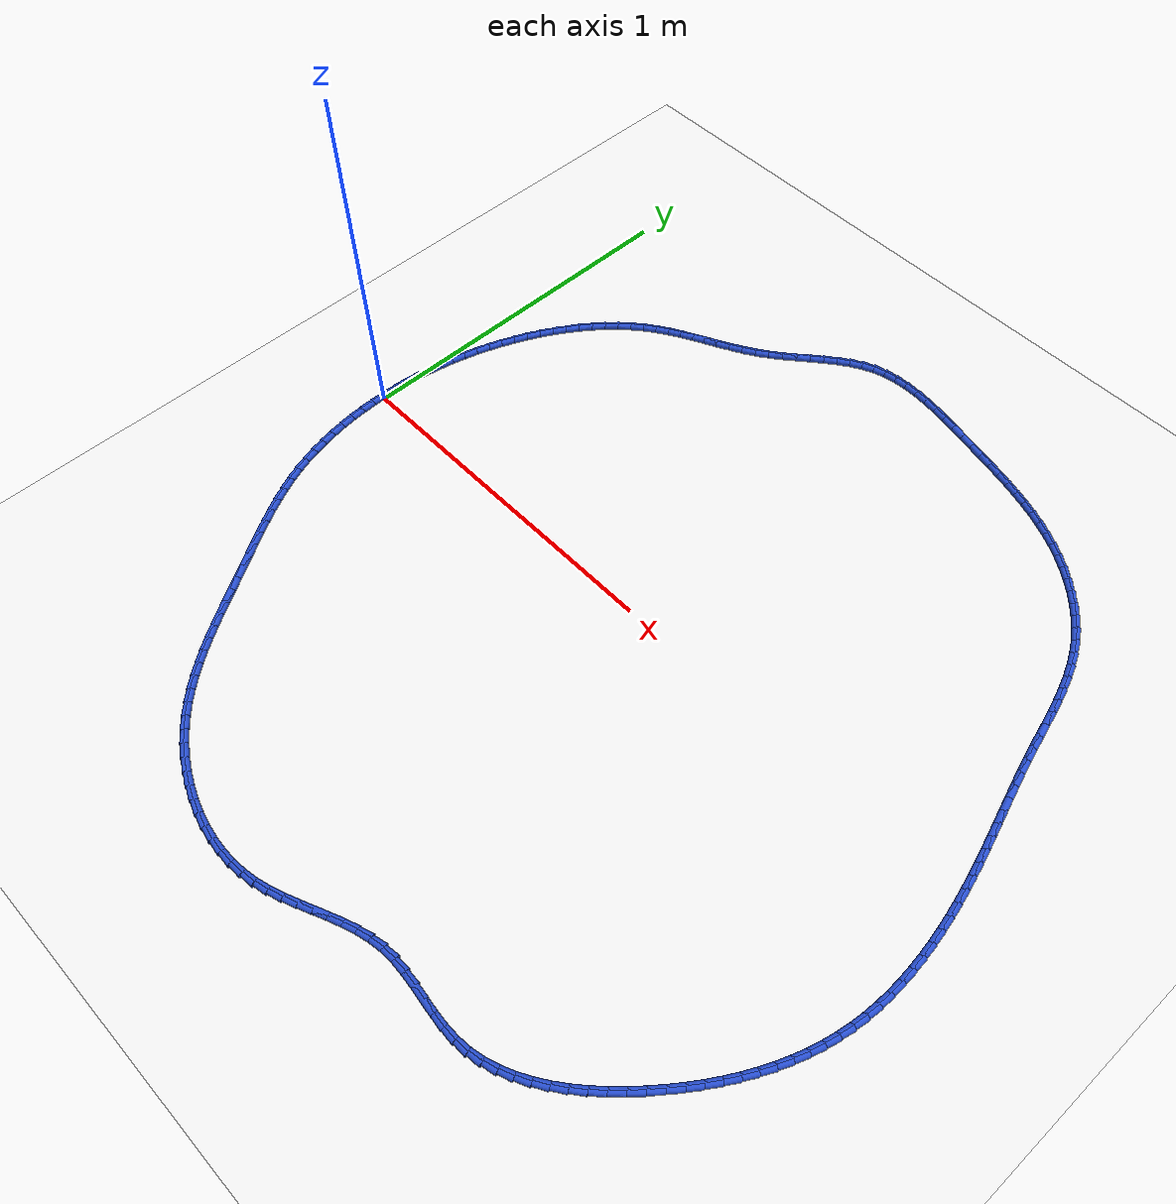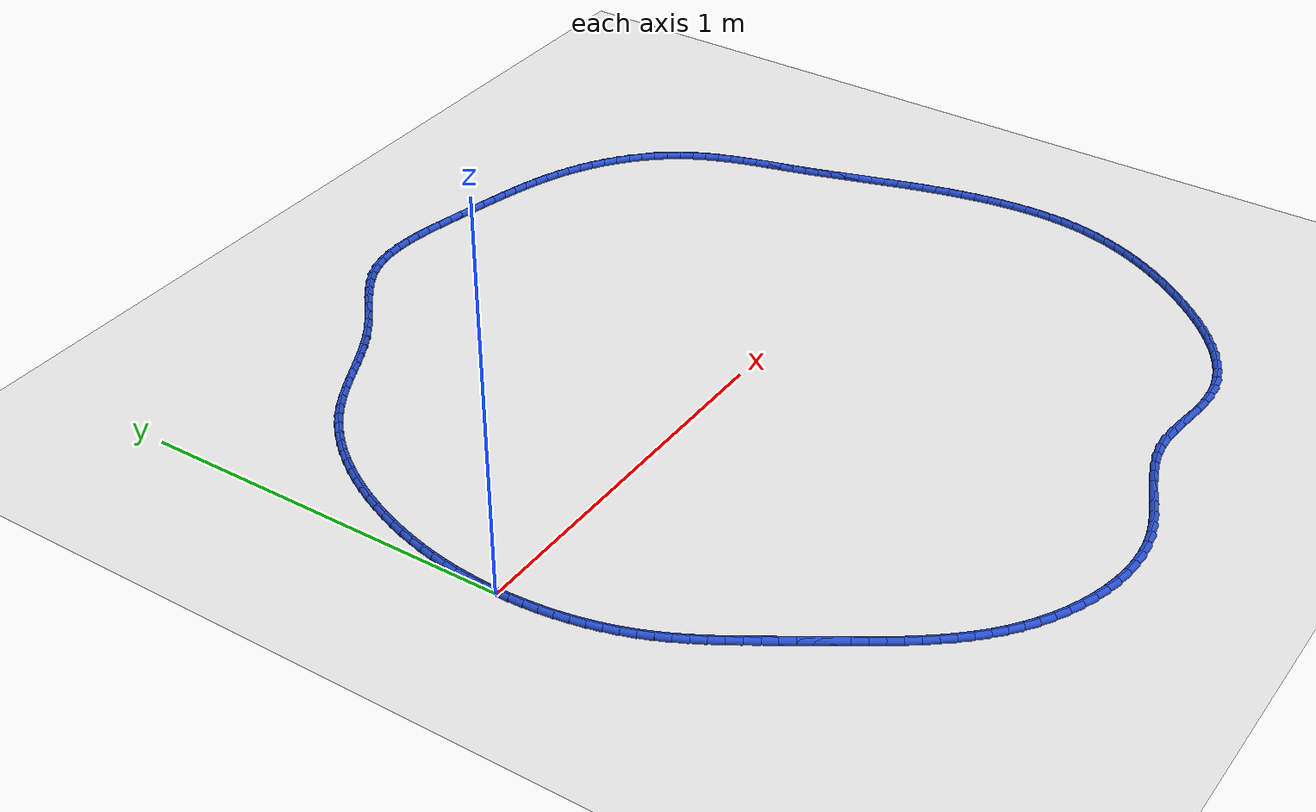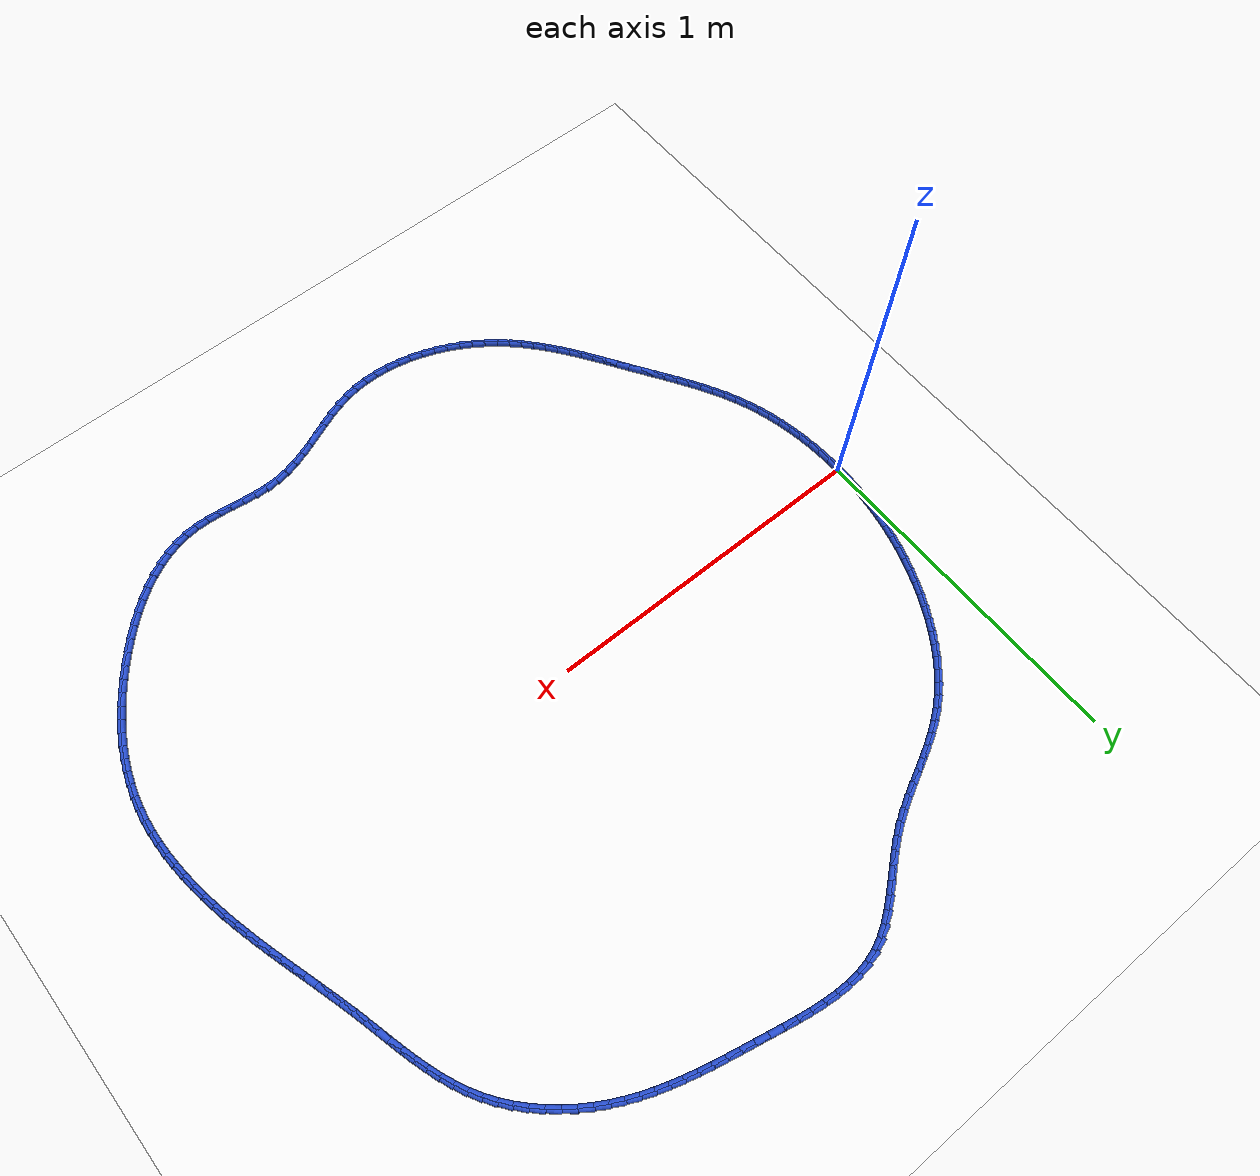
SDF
<sdf version="1.6">
 <world name="default">
  <light name="sun" type="directional">
   <pose>0 0 10 0 -0 0</pose>
   <diffuse>0.8 0.8 0.8 1</diffuse>
   <specular>0.2 0.2 0.2 1</specular>
   <attenuation>
    <range>1000</range>
    <constant>0.9</constant>
    <linear>0.01</linear>
    <quadratic>0.001</quadratic>
   </attenuation>
   <direction>-0.5 0.1 -0.9</direction>
  </light>
  <model name="ground_plane">
   <static>1</static>
   <link name="link">
    <collision name="collision">
     <geometry><plane><normal>0 0 1</normal><size>100 100</size></plane></geometry>
     <surface><friction><ode><mu>100</mu><mu2>50</mu2></ode></friction></surface>
    </collision>
    <visual name="visual">
     <cast_shadows>0</cast_shadows>
     <geometry><plane><normal>0 0 1</normal><size>100 100</size></plane></geometry>
     <material>
      <script><uri>file://media/materials/scripts/gazebo.material</uri><name>Gazebo/WhiteGlow</name></script>
     </material>
    </visual>
   </link>
  </model>
  <gravity>0 0 -9.8</gravity>
  <magnetic_field>6e-06 2.3e-05 -4.2e-05</magnetic_field>
  <atmosphere type="adiabatic"/>
  <physics name="default_physics" default="0" type="ode">
   <max_step_size>0.001</max_step_size>
   <real_time_factor>1</real_time_factor>
   <real_time_update_rate>1000</real_time_update_rate>
  </physics>
  <scene><ambient>0.4 0.4 0.4 1</ambient><background>0.7 0.7 0.7 1</background><shadows>1</shadows></scene>
  <spherical_coordinates>
   <surface_model>EARTH_WGS84</surface_model>
   <latitude_deg>0</latitude_deg>
   <longitude_deg>0</longitude_deg>
   <elevation>0</elevation>
   <heading_deg>0</heading_deg>
  </spherical_coordinates>
  <model name="line">
   <link name="link_0">
    <pose>1.474514954580286e-17 6.938893903907228e-18 0.01 0 1.57 1.545686650582758</pose>
    <collision name="collision">
     <geometry><cylinder><radius>0.01</radius><length>0.08</length></cylinder></geometry>
    </collision>
    <visual name="visual">
     <material>
      <script><name>Gazebo/Blue</name><uri>file://media/materials/scripts/gazebo.material</uri></script>
     </material>
     <geometry><cylinder><radius>0.01</radius><length>0.08</length></cylinder></geometry>
    </visual>
   </link>
   <link name="link_1">
    <pose>0.0009447311950475684 0.03761628103148649 0.01 0 1.57 1.5097009069602436</pose>
    <collision name="collision">
     <geometry><cylinder><radius>0.01</radius><length>0.08</length></cylinder></geometry>
    </collision>
    <visual name="visual">
     <material>
      <script><name>Gazebo/Blue</name><uri>file://media/materials/scripts/gazebo.material</uri></script>
     </material>
     <geometry><cylinder><radius>0.01</radius><length>0.08</length></cylinder></geometry>
    </visual>
   </link>
   <link name="link_2">
    <pose>0.0032360933093642926 0.07507425185217446 0.01 0 1.57 1.4735485353333542</pose>
    <collision name="collision">
     <geometry><cylinder><radius>0.01</radius><length>0.08</length></cylinder></geometry>
    </collision>
    <visual name="visual">
     <material>
      <script><name>Gazebo/Blue</name><uri>file://media/materials/scripts/gazebo.material</uri></script>
     </material>
     <geometry><cylinder><radius>0.01</radius><length>0.08</length></cylinder></geometry>
    </visual>
   </link>
   <link name="link_3">
    <pose>0.006874574108960455 0.11237076667838555 0.01 0 1.57 1.437314409622422</pose>
    <collision name="collision">
     <geometry><cylinder><radius>0.01</radius><length>0.08</length></cylinder></geometry>
    </collision>
    <visual name="visual">
     <material>
      <script><name>Gazebo/Blue</name><uri>file://media/materials/scripts/gazebo.material</uri></script>
     </material>
     <geometry><cylinder><radius>0.01</radius><length>0.08</length></cylinder></geometry>
    </visual>
   </link>
   <link name="link_4">
    <pose>0.011860661359846331 0.1495026797264415 0.01 0 1.57 1.4010846129707828</pose>
    <collision name="collision">
     <geometry><cylinder><radius>0.01</radius><length>0.08</length></cylinder></geometry>
    </collision>
    <visual name="visual">
     <material>
      <script><name>Gazebo/Blue</name><uri>file://media/materials/scripts/gazebo.material</uri></script>
     </material>
     <geometry><cylinder><radius>0.01</radius><length>0.08</length></cylinder></geometry>
    </visual>
   </link>
   <link name="link_5">
    <pose>0.018194842828032184 0.18646684521266396 0.01 0 1.57 1.3649451765406557</pose>
    <collision name="collision">
     <geometry><cylinder><radius>0.01</radius><length>0.08</length></cylinder></geometry>
    </collision>
    <visual name="visual">
     <material>
      <script><name>Gazebo/Blue</name><uri>file://media/materials/scripts/gazebo.material</uri></script>
     </material>
     <geometry><cylinder><radius>0.01</radius><length>0.08</length></cylinder></geometry>
    </visual>
   </link>
   <link name="link_6">
    <pose>0.025877606279528273 0.22326011735337453 0.01 0 1.57 1.3289808202071065</pose>
    <collision name="collision">
     <geometry><cylinder><radius>0.01</radius><length>0.08</length></cylinder></geometry>
    </collision>
    <visual name="visual">
     <material>
      <script><name>Gazebo/Blue</name><uri>file://media/materials/scripts/gazebo.material</uri></script>
     </material>
     <geometry><cylinder><radius>0.01</radius><length>0.08</length></cylinder></geometry>
    </visual>
   </link>
   <link name="link_7">
    <pose>0.03490943948034488 0.259879350364895 0.01 0 1.57 1.2932737408723436</pose>
    <collision name="collision">
     <geometry><cylinder><radius>0.01</radius><length>0.08</length></cylinder></geometry>
    </collision>
    <visual name="visual">
     <material>
      <script><name>Gazebo/Blue</name><uri>file://media/materials/scripts/gazebo.material</uri></script>
     </material>
     <geometry><cylinder><radius>0.01</radius><length>0.08</length></cylinder></geometry>
    </visual>
   </link>
   <link name="link_8">
    <pose>0.04529083019649228 0.296321398463547 0.01 0 1.57 1.2579024909270795</pose>
    <collision name="collision">
     <geometry><cylinder><radius>0.01</radius><length>0.08</length></cylinder></geometry>
    </collision>
    <visual name="visual">
     <material>
      <script><name>Gazebo/Blue</name><uri>file://media/materials/scripts/gazebo.material</uri></script>
     </material>
     <geometry><cylinder><radius>0.01</radius><length>0.08</length></cylinder></geometry>
    </visual>
   </link>
   <link name="link_9">
    <pose>0.05702226619398071 0.33258311586565226 0.01 0 1.57 1.2228334082370127</pose>
    <collision name="collision">
     <geometry><cylinder><radius>0.01</radius><length>0.08</length></cylinder></geometry>
    </collision>
    <visual name="visual">
     <material>
      <script><name>Gazebo/Blue</name><uri>file://media/materials/scripts/gazebo.material</uri></script>
     </material>
     <geometry><cylinder><radius>0.01</radius><length>0.08</length></cylinder></geometry>
    </visual>
   </link>
   <link name="link_10">
    <pose>0.07010474169398115 0.3686506457477198 0.01 0 1.57 1.187064248298604</pose>
    <collision name="collision">
     <geometry><cylinder><radius>0.01</radius><length>0.08</length></cylinder></geometry>
    </collision>
    <visual name="visual">
     <material>
      <script><name>Gazebo/Blue</name><uri>file://media/materials/scripts/gazebo.material</uri></script>
     </material>
     <geometry><cylinder><radius>0.01</radius><length>0.08</length></cylinder></geometry>
    </visual>
   </link>
   <link name="link_11">
    <pose>0.08454382571492287 0.4044133787218165 0.01 0 1.57 1.149817026023047</pose>
    <collision name="collision">
     <geometry><cylinder><radius>0.01</radius><length>0.08</length></cylinder></geometry>
    </collision>
    <visual name="visual">
     <material>
      <script><name>Gazebo/Blue</name><uri>file://media/materials/scripts/gazebo.material</uri></script>
     </material>
     <geometry><cylinder><radius>0.01</radius><length>0.08</length></cylinder></geometry>
    </visual>
   </link>
   <link name="link_12">
    <pose>0.10034751541647847 0.4397093525467908 0.01 0 1.57 1.1107800819667435</pose>
    <collision name="collision">
     <geometry><cylinder><radius>0.01</radius><length>0.08</length></cylinder></geometry>
    </collision>
    <visual name="visual">
     <material>
      <script><name>Gazebo/Blue</name><uri>file://media/materials/scripts/gazebo.material</uri></script>
     </material>
     <geometry><cylinder><radius>0.01</radius><length>0.08</length></cylinder></geometry>
    </visual>
   </link>
   <link name="link_13">
    <pose>0.11752383029660916 0.47437613254816313 0.01 0 1.57 1.0696403028857504</pose>
    <collision name="collision">
     <geometry><cylinder><radius>0.01</radius><length>0.08</length></cylinder></geometry>
    </collision>
    <visual name="visual">
     <material>
      <script><name>Gazebo/Blue</name><uri>file://media/materials/scripts/gazebo.material</uri></script>
     </material>
     <geometry><cylinder><radius>0.01</radius><length>0.08</length></cylinder></geometry>
    </visual>
   </link>
   <link name="link_14">
    <pose>0.13608078985327582 0.5082512840514536 0.01 0 1.57 1.0260779592216136</pose>
    <collision name="collision">
     <geometry><cylinder><radius>0.01</radius><length>0.08</length></cylinder></geometry>
    </collision>
    <visual name="visual">
     <material>
      <script><name>Gazebo/Blue</name><uri>file://media/materials/scripts/gazebo.material</uri></script>
     </material>
     <geometry><cylinder><radius>0.01</radius><length>0.08</length></cylinder></geometry>
    </visual>
   </link>
   <link name="link_15">
    <pose>0.15602641358443975 0.5411723723821834 0.01 0 1.57 0.9797687786360625</pose>
    <collision name="collision">
     <geometry><cylinder><radius>0.01</radius><length>0.08</length></cylinder></geometry>
    </collision>
    <visual name="visual">
     <material>
      <script><name>Gazebo/Blue</name><uri>file://media/materials/scripts/gazebo.material</uri></script>
     </material>
     <geometry><cylinder><radius>0.01</radius><length>0.08</length></cylinder></geometry>
    </visual>
   </link>
   <link name="link_16">
    <pose>0.1773687209880618 0.5729769628658722 0.01 0 1.57 0.9303892517088639</pose>
    <collision name="collision">
     <geometry><cylinder><radius>0.01</radius><length>0.08</length></cylinder></geometry>
    </collision>
    <visual name="visual">
     <material>
      <script><name>Gazebo/Blue</name><uri>file://media/materials/scripts/gazebo.material</uri></script>
     </material>
     <geometry><cylinder><radius>0.01</radius><length>0.08</length></cylinder></geometry>
    </visual>
   </link>
   <link name="link_17">
    <pose>0.20011573156210302 0.6035026208280406 0.01 0 1.57 0.8776261070844655</pose>
    <collision name="collision">
     <geometry><cylinder><radius>0.01</radius><length>0.08</length></cylinder></geometry>
    </collision>
    <visual name="visual">
     <material>
      <script><name>Gazebo/Blue</name><uri>file://media/materials/scripts/gazebo.material</uri></script>
     </material>
     <geometry><cylinder><radius>0.01</radius><length>0.08</length></cylinder></geometry>
    </visual>
   </link>
   <link name="link_18">
    <pose>0.22427546480452476 0.6325869115942094 0.01 0 1.57 0.8211909925810428</pose>
    <collision name="collision">
     <geometry><cylinder><radius>0.01</radius><length>0.08</length></cylinder></geometry>
    </collision>
    <visual name="visual">
     <material>
      <script><name>Gazebo/Blue</name><uri>file://media/materials/scripts/gazebo.material</uri></script>
     </material>
     <geometry><cylinder><radius>0.01</radius><length>0.08</length></cylinder></geometry>
    </visual>
   </link>
   <link name="link_19">
    <pose>0.2498559402132878 0.660067400489899 0.01 0 1.57 0.7608412834058123</pose>
    <collision name="collision">
     <geometry><cylinder><radius>0.01</radius><length>0.08</length></cylinder></geometry>
    </collision>
    <visual name="visual">
     <material>
      <script><name>Gazebo/Blue</name><uri>file://media/materials/scripts/gazebo.material</uri></script>
     </material>
     <geometry><cylinder><radius>0.01</radius><length>0.08</length></cylinder></geometry>
    </visual>
   </link>
   <link name="link_20">
    <pose>0.2768651772863534 0.6857816528406295 0.01 0 1.57 0.69640743524502</pose>
    <collision name="collision">
     <geometry><cylinder><radius>0.01</radius><length>0.08</length></cylinder></geometry>
    </collision>
    <visual name="visual">
     <material>
      <script><name>Gazebo/Blue</name><uri>file://media/materials/scripts/gazebo.material</uri></script>
     </material>
     <geometry><cylinder><radius>0.01</radius><length>0.08</length></cylinder></geometry>
    </visual>
   </link>
   <link name="link_21">
    <pose>0.3053111955216825 0.7095672339719219 0.01 0 1.57 0.6280464921986971</pose>
    <collision name="collision">
     <geometry><cylinder><radius>0.01</radius><length>0.08</length></cylinder></geometry>
    </collision>
    <visual name="visual">
     <material>
      <script><name>Gazebo/Blue</name><uri>file://media/materials/scripts/gazebo.material</uri></script>
     </material>
     <geometry><cylinder><radius>0.01</radius><length>0.08</length></cylinder></geometry>
    </visual>
   </link>
   <link name="link_22">
    <pose>0.33519863604031175 0.731269310664203 0.01 0 1.57 0.5638640659860605</pose>
    <collision name="collision">
     <geometry><cylinder><radius>0.01</radius><length>0.08</length></cylinder></geometry>
    </collision>
    <visual name="visual">
     <material>
      <script><name>Gazebo/Blue</name><uri>file://media/materials/scripts/gazebo.material</uri></script>
     </material>
     <geometry><cylinder><radius>0.01</radius><length>0.08</length></cylinder></geometry>
    </visual>
   </link>
   <link name="link_23">
    <pose>0.36641076022891167 0.7510061579383303 0.01 0 1.57 0.5143066194858495</pose>
    <collision name="collision">
     <geometry><cylinder><radius>0.01</radius><length>0.08</length></cylinder></geometry>
    </collision>
    <visual name="visual">
     <material>
      <script><name>Gazebo/Blue</name><uri>file://media/materials/scripts/gazebo.material</uri></script>
     </material>
     <geometry><cylinder><radius>0.01</radius><length>0.08</length></cylinder></geometry>
    </visual>
   </link>
   <link name="link_24">
    <pose>0.39867868164184384 0.769238388248872 0.01 0 1.57 0.4801477147695534</pose>
    <collision name="collision">
     <geometry><cylinder><radius>0.01</radius><length>0.08</length></cylinder></geometry>
    </collision>
    <visual name="visual">
     <material>
      <script><name>Gazebo/Blue</name><uri>file://media/materials/scripts/gazebo.material</uri></script>
     </material>
     <geometry><cylinder><radius>0.01</radius><length>0.08</length></cylinder></geometry>
    </visual>
   </link>
   <link name="link_25">
    <pose>0.43172388320487454 0.7864482832692636 0.01 0 1.57 0.4612086540856606</pose>
    <collision name="collision">
     <geometry><cylinder><radius>0.01</radius><length>0.08</length></cylinder></geometry>
    </collision>
    <visual name="visual">
     <material>
      <script><name>Gazebo/Blue</name><uri>file://media/materials/scripts/gazebo.material</uri></script>
     </material>
     <geometry><cylinder><radius>0.01</radius><length>0.08</length></cylinder></geometry>
    </visual>
   </link>
   <link name="link_26">
    <pose>0.46526784784376946 0.80311812467294 0.01 0 1.57 0.4572290072283732</pose>
    <collision name="collision">
     <geometry><cylinder><radius>0.01</radius><length>0.08</length></cylinder></geometry>
    </collision>
    <visual name="visual">
     <material>
      <script><name>Gazebo/Blue</name><uri>file://media/materials/scripts/gazebo.material</uri></script>
     </material>
     <geometry><cylinder><radius>0.01</radius><length>0.08</length></cylinder></geometry>
    </visual>
   </link>
   <link name="link_27">
    <pose>0.49903205848429427 0.8197301941333361 0.01 0 1.57 0.467996018739926</pose>
    <collision name="collision">
     <geometry><cylinder><radius>0.01</radius><length>0.08</length></cylinder></geometry>
    </collision>
    <visual name="visual">
     <material>
      <script><name>Gazebo/Blue</name><uri>file://media/materials/scripts/gazebo.material</uri></script>
     </material>
     <geometry><cylinder><radius>0.01</radius><length>0.08</length></cylinder></geometry>
    </visual>
   </link>
   <link name="link_28">
    <pose>0.5327379980522156 0.836766773323888 0.01 0 1.57 0.49336889712530657</pose>
    <collision name="collision">
     <geometry><cylinder><radius>0.01</radius><length>0.08</length></cylinder></geometry>
    </collision>
    <visual name="visual">
     <material>
      <script><name>Gazebo/Blue</name><uri>file://media/materials/scripts/gazebo.material</uri></script>
     </material>
     <geometry><cylinder><radius>0.01</radius><length>0.08</length></cylinder></geometry>
    </visual>
   </link>
   <link name="link_29">
    <pose>0.5661071494732987 0.85471014391803 0.01 0 1.57 0.533207896753018</pose>
    <collision name="collision">
     <geometry><cylinder><radius>0.01</radius><length>0.08</length></cylinder></geometry>
    </collision>
    <visual name="visual">
     <material>
      <script><name>Gazebo/Blue</name><uri>file://media/materials/scripts/gazebo.material</uri></script>
     </material>
     <geometry><cylinder><radius>0.01</radius><length>0.08</length></cylinder></geometry>
    </visual>
   </link>
   <link name="link_30">
    <pose>0.5988609956733096 0.8740425875891977 0.01 0 1.57 0.5871613968589999</pose>
    <collision name="collision">
     <geometry><cylinder><radius>0.01</radius><length>0.08</length></cylinder></geometry>
    </collision>
    <visual name="visual">
     <material>
      <script><name>Gazebo/Blue</name><uri>file://media/materials/scripts/gazebo.material</uri></script>
     </material>
     <geometry><cylinder><radius>0.01</radius><length>0.08</length></cylinder></geometry>
    </visual>
   </link>
   <link name="link_31">
    <pose>0.6307218846848133 0.8952444885408729 0.01 0 1.57 0.6440316544857898</pose>
    <collision name="collision">
     <geometry><cylinder><radius>0.01</radius><length>0.08</length></cylinder></geometry>
    </collision>
    <visual name="visual">
     <material>
      <script><name>Gazebo/Blue</name><uri>file://media/materials/scripts/gazebo.material</uri></script>
     </material>
     <geometry><cylinder><radius>0.01</radius><length>0.08</length></cylinder></geometry>
    </visual>
   </link>
   <link name="link_32">
    <pose>0.6615849064864272 0.918417349834066 0.01 0 1.57 0.6807557867257129</pose>
    <collision name="collision">
     <geometry><cylinder><radius>0.01</radius><length>0.08</length></cylinder></geometry>
    </collision>
    <visual name="visual">
     <material>
      <script><name>Gazebo/Blue</name><uri>file://media/materials/scripts/gazebo.material</uri></script>
     </material>
     <geometry><cylinder><radius>0.01</radius><length>0.08</length></cylinder></geometry>
    </visual>
   </link>
   <link name="link_33">
    <pose>0.6917254528583263 0.9428285448678801 0.01 0 1.57 0.6951146268430668</pose>
    <collision name="collision">
     <geometry><cylinder><radius>0.01</radius><length>0.08</length></cylinder></geometry>
    </collision>
    <visual name="visual">
     <material>
      <script><name>Gazebo/Blue</name><uri>file://media/materials/scripts/gazebo.material</uri></script>
     </material>
     <geometry><cylinder><radius>0.01</radius><length>0.08</length></cylinder></geometry>
    </visual>
   </link>
   <link name="link_34">
    <pose>0.7214695904114714 0.9676343001068053 0.01 0 1.57 0.6873016695418545</pose>
    <collision name="collision">
     <geometry><cylinder><radius>0.01</radius><length>0.08</length></cylinder></geometry>
    </collision>
    <visual name="visual">
     <material>
      <script><name>Gazebo/Blue</name><uri>file://media/materials/scripts/gazebo.material</uri></script>
     </material>
     <geometry><cylinder><radius>0.01</radius><length>0.08</length></cylinder></geometry>
    </visual>
   </link>
   <link name="link_35">
    <pose>0.7511433857568239 0.991990842015331 0.01 0 1.57 0.6565524947184433</pose>
    <collision name="collision">
     <geometry><cylinder><radius>0.01</radius><length>0.08</length></cylinder></geometry>
    </collision>
    <visual name="visual">
     <material>
      <script><name>Gazebo/Blue</name><uri>file://media/materials/scripts/gazebo.material</uri></script>
     </material>
     <geometry><cylinder><radius>0.01</radius><length>0.08</length></cylinder></geometry>
    </visual>
   </link>
   <link name="link_36">
    <pose>0.7810729055053458 1.0150543970579475 0.01 0 1.57 0.6011797031705326</pose>
    <collision name="collision">
     <geometry><cylinder><radius>0.01</radius><length>0.08</length></cylinder></geometry>
    </collision>
    <visual name="visual">
     <material>
      <script><name>Gazebo/Blue</name><uri>file://media/materials/scripts/gazebo.material</uri></script>
     </material>
     <geometry><cylinder><radius>0.01</radius><length>0.08</length></cylinder></geometry>
    </visual>
   </link>
   <link name="link_37">
    <pose>0.8115842162679975 1.0359811916991446 0.01 0 1.57 0.5189649516195042</pose>
    <collision name="collision">
     <geometry><cylinder><radius>0.01</radius><length>0.08</length></cylinder></geometry>
    </collision>
    <visual name="visual">
     <material>
      <script><name>Gazebo/Blue</name><uri>file://media/materials/scripts/gazebo.material</uri></script>
     </material>
     <geometry><cylinder><radius>0.01</radius><length>0.08</length></cylinder></geometry>
    </visual>
   </link>
   <link name="link_38">
    <pose>0.8430033846557405 1.0539274524034117 0.01 0 1.57 0.40819293050368466</pose>
    <collision name="collision">
     <geometry><cylinder><radius>0.01</radius><length>0.08</length></cylinder></geometry>
    </collision>
    <visual name="visual">
     <material>
      <script><name>Gazebo/Blue</name><uri>file://media/materials/scripts/gazebo.material</uri></script>
     </material>
     <geometry><cylinder><radius>0.01</radius><length>0.08</length></cylinder></geometry>
    </visual>
   </link>
   <link name="link_39">
    <pose>0.875656476687202 1.0680494071366773 0.01 0 1.57 0.2768907122084179</pose>
    <collision name="collision">
     <geometry><cylinder><radius>0.01</radius><length>0.08</length></cylinder></geometry>
    </collision>
    <visual name="visual">
     <material>
      <script><name>Gazebo/Blue</name><uri>file://media/materials/scripts/gazebo.material</uri></script>
     </material>
     <geometry><cylinder><radius>0.01</radius><length>0.08</length></cylinder></geometry>
    </visual>
   </link>
   <link name="link_40">
    <pose>0.9097740729027157 1.0777453187078059 0.01 0 1.57 0.1562112137187419</pose>
    <collision name="collision">
     <geometry><cylinder><radius>0.01</radius><length>0.08</length></cylinder></geometry>
    </collision>
    <visual name="visual">
     <material>
      <script><name>Gazebo/Blue</name><uri>file://media/materials/scripts/gazebo.material</uri></script>
     </material>
     <geometry><cylinder><radius>0.01</radius><length>0.08</length></cylinder></geometry>
    </visual>
   </link>
   <link name="link_41">
    <pose>0.9452256601136987 1.0833287437014865 0.01 0 1.57 0.05465799892209218</pose>
    <collision name="collision">
     <geometry><cylinder><radius>0.01</radius><length>0.08</length></cylinder></geometry>
    </collision>
    <visual name="visual">
     <material>
      <script><name>Gazebo/Blue</name><uri>file://media/materials/scripts/gazebo.material</uri></script>
     </material>
     <geometry><cylinder><radius>0.01</radius><length>0.08</length></cylinder></geometry>
    </visual>
   </link>
   <link name="link_42">
    <pose>0.9817953821972434 1.0853295644105112 0.01 0 1.57 -0.028064290250514535</pose>
    <collision name="collision">
     <geometry><cylinder><radius>0.01</radius><length>0.08</length></cylinder></geometry>
    </collision>
    <visual name="visual">
     <material>
      <script><name>Gazebo/Blue</name><uri>file://media/materials/scripts/gazebo.material</uri></script>
     </material>
     <geometry><cylinder><radius>0.01</radius><length>0.08</length></cylinder></geometry>
    </visual>
   </link>
   <link name="link_43">
    <pose>1.019267383030441 1.084277663127671 0.01 0 1.57 -0.09340894597363829</pose>
    <collision name="collision">
     <geometry><cylinder><radius>0.01</radius><length>0.08</length></cylinder></geometry>
    </collision>
    <visual name="visual">
     <material>
      <script><name>Gazebo/Blue</name><uri>file://media/materials/scripts/gazebo.material</uri></script>
     </material>
     <geometry><cylinder><radius>0.01</radius><length>0.08</length></cylinder></geometry>
    </visual>
   </link>
   <link name="link_44">
    <pose>1.0574258064903836 1.0807029221457571 0.01 0 1.57 -0.14314682011853433</pose>
    <collision name="collision">
     <geometry><cylinder><radius>0.01</radius><length>0.08</length></cylinder></geometry>
    </collision>
    <visual name="visual">
     <material>
      <script><name>Gazebo/Blue</name><uri>file://media/materials/scripts/gazebo.material</uri></script>
     </material>
     <geometry><cylinder><radius>0.01</radius><length>0.08</length></cylinder></geometry>
    </visual>
   </link>
   <link name="link_45">
    <pose>1.0960547964541636 1.0751352237575615 0.01 0 1.57 -0.17888267754836734</pose>
    <collision name="collision">
     <geometry><cylinder><radius>0.01</radius><length>0.08</length></cylinder></geometry>
    </collision>
    <visual name="visual">
     <material>
      <script><name>Gazebo/Blue</name><uri>file://media/materials/scripts/gazebo.material</uri></script>
     </material>
     <geometry><cylinder><radius>0.01</radius><length>0.08</length></cylinder></geometry>
    </visual>
   </link>
   <link name="link_46">
    <pose>1.1349384967988727 1.0681044502558752 0.01 0 1.57 -0.20182484992709407</pose>
    <collision name="collision">
     <geometry><cylinder><radius>0.01</radius><length>0.08</length></cylinder></geometry>
    </collision>
    <visual name="visual">
     <material>
      <script><name>Gazebo/Blue</name><uri>file://media/materials/scripts/gazebo.material</uri></script>
     </material>
     <geometry><cylinder><radius>0.01</radius><length>0.08</length></cylinder></geometry>
    </visual>
   </link>
   <link name="link_47">
    <pose>1.1738610514016017 1.0601404839334896 0.01 0 1.57 -0.21268831791208223</pose>
    <collision name="collision">
     <geometry><cylinder><radius>0.01</radius><length>0.08</length></cylinder></geometry>
    </collision>
    <visual name="visual">
     <material>
      <script><name>Gazebo/Blue</name><uri>file://media/materials/scripts/gazebo.material</uri></script>
     </material>
     <geometry><cylinder><radius>0.01</radius><length>0.08</length></cylinder></geometry>
    </visual>
   </link>
   <link name="link_48">
    <pose>1.2126066041394439 1.0517732070831967 0.01 0 1.57 -0.21323765566338074</pose>
    <collision name="collision">
     <geometry><cylinder><radius>0.01</radius><length>0.08</length></cylinder></geometry>
    </collision>
    <visual name="visual">
     <material>
      <script><name>Gazebo/Blue</name><uri>file://media/materials/scripts/gazebo.material</uri></script>
     </material>
     <geometry><cylinder><radius>0.01</radius><length>0.08</length></cylinder></geometry>
    </visual>
   </link>
   <link name="link_49">
    <pose>1.2509776631504053 1.0434647395188101 0.01 0 1.57 -0.21430568211302622</pose>
    <collision name="collision">
     <geometry><cylinder><radius>0.01</radius><length>0.08</length></cylinder></geometry>
    </collision>
    <visual name="visual">
     <material>
      <script><name>Gazebo/Blue</name><uri>file://media/materials/scripts/gazebo.material</uri></script>
     </material>
     <geometry><cylinder><radius>0.01</radius><length>0.08</length></cylinder></geometry>
    </visual>
   </link>
   <link name="link_50">
    <pose>1.2889032679867423 1.0352103114614886 0.01 0 1.57 -0.22062290532530543</pose>
    <collision name="collision">
     <geometry><cylinder><radius>0.01</radius><length>0.08</length></cylinder></geometry>
    </collision>
    <visual name="visual">
     <material>
      <script><name>Gazebo/Blue</name><uri>file://media/materials/scripts/gazebo.material</uri></script>
     </material>
     <geometry><cylinder><radius>0.01</radius><length>0.08</length></cylinder></geometry>
    </visual>
   </link>
   <link name="link_51">
    <pose>1.3263657627437275 1.0268084641399922 0.01 0 1.57 -0.23236589635160992</pose>
    <collision name="collision">
     <geometry><cylinder><radius>0.01</radius><length>0.08</length></cylinder></geometry>
    </collision>
    <visual name="visual">
     <material>
      <script><name>Gazebo/Blue</name><uri>file://media/materials/scripts/gazebo.material</uri></script>
     </material>
     <geometry><cylinder><radius>0.01</radius><length>0.08</length></cylinder></geometry>
    </visual>
   </link>
   <link name="link_52">
    <pose>1.363347677998478 1.0180570506817679 0.01 0 1.57 -0.24967230393669435</pose>
    <collision name="collision">
     <geometry><cylinder><radius>0.01</radius><length>0.08</length></cylinder></geometry>
    </collision>
    <visual name="visual">
     <material>
      <script><name>Gazebo/Blue</name><uri>file://media/materials/scripts/gazebo.material</uri></script>
     </material>
     <geometry><cylinder><radius>0.01</radius><length>0.08</length></cylinder></geometry>
    </visual>
   </link>
   <link name="link_53">
    <pose>1.399831544328109 1.0087539242142645 0.01 0 1.57 -0.27264383680383425</pose>
    <collision name="collision">
     <geometry><cylinder><radius>0.01</radius><length>0.08</length></cylinder></geometry>
    </collision>
    <visual name="visual">
     <material>
      <script><name>Gazebo/Blue</name><uri>file://media/materials/scripts/gazebo.material</uri></script>
     </material>
     <geometry><cylinder><radius>0.01</radius><length>0.08</length></cylinder></geometry>
    </visual>
   </link>
   <link name="link_54">
    <pose>1.4357998923097375 0.9986969378649291 0.01 0 1.57 -0.30132721122784484</pose>
    <collision name="collision">
     <geometry><cylinder><radius>0.01</radius><length>0.08</length></cylinder></geometry>
    </collision>
    <visual name="visual">
     <material>
      <script><name>Gazebo/Blue</name><uri>file://media/materials/scripts/gazebo.material</uri></script>
     </material>
     <geometry><cylinder><radius>0.01</radius><length>0.08</length></cylinder></geometry>
    </visual>
   </link>
   <link name="link_55">
    <pose>1.4712352525204806 0.98768394476121 0.01 0 1.57 -0.3356895209946991</pose>
    <collision name="collision">
     <geometry><cylinder><radius>0.01</radius><length>0.08</length></cylinder></geometry>
    </collision>
    <visual name="visual">
     <material>
      <script><name>Gazebo/Blue</name><uri>file://media/materials/scripts/gazebo.material</uri></script>
     </material>
     <geometry><cylinder><radius>0.01</radius><length>0.08</length></cylinder></geometry>
    </visual>
   </link>
   <link name="link_56">
    <pose>1.5061201555374533 0.9755127980305555 0.01 0 1.57 -0.37558959024129496</pose>
    <collision name="collision">
     <geometry><cylinder><radius>0.01</radius><length>0.08</length></cylinder></geometry>
    </collision>
    <visual name="visual">
     <material>
      <script><name>Gazebo/Blue</name><uri>file://media/materials/scripts/gazebo.material</uri></script>
     </material>
     <geometry><cylinder><radius>0.01</radius><length>0.08</length></cylinder></geometry>
    </visual>
   </link>
   <link name="link_57">
    <pose>1.5404371319377734 0.9619813508004131 0.01 0 1.57 -0.4207485864366747</pose>
    <collision name="collision">
     <geometry><cylinder><radius>0.01</radius><length>0.08</length></cylinder></geometry>
    </collision>
    <visual name="visual">
     <material>
      <script><name>Gazebo/Blue</name><uri>file://media/materials/scripts/gazebo.material</uri></script>
     </material>
     <geometry><cylinder><radius>0.01</radius><length>0.08</length></cylinder></geometry>
    </visual>
   </link>
   <link name="link_58">
    <pose>1.5741687122985564 0.9468874561982309 0.01 0 1.57 -0.4707251097073771</pose>
    <collision name="collision">
     <geometry><cylinder><radius>0.01</radius><length>0.08</length></cylinder></geometry>
    </collision>
    <visual name="visual">
     <material>
      <script><name>Gazebo/Blue</name><uri>file://media/materials/scripts/gazebo.material</uri></script>
     </material>
     <geometry><cylinder><radius>0.01</radius><length>0.08</length></cylinder></geometry>
    </visual>
   </link>
   <link name="link_59">
    <pose>1.6072974271969185 0.9300289673514566 0.01 0 1.57 -0.5246531406020764</pose>
    <collision name="collision">
     <geometry><cylinder><radius>0.01</radius><length>0.08</length></cylinder></geometry>
    </collision>
    <visual name="visual">
     <material>
      <script><name>Gazebo/Blue</name><uri>file://media/materials/scripts/gazebo.material</uri></script>
     </material>
     <geometry><cylinder><radius>0.01</radius><length>0.08</length></cylinder></geometry>
    </visual>
   </link>
   <link name="link_60">
    <pose>1.6397892204547773 0.911224116315038 0.01 0 1.57 -0.5800681598573565</pose>
    <collision name="collision">
     <geometry><cylinder><radius>0.01</radius><length>0.08</length></cylinder></geometry>
    </collision>
    <visual name="visual">
     <material>
      <script><name>Gazebo/Blue</name><uri>file://media/materials/scripts/gazebo.material</uri></script>
     </material>
     <geometry><cylinder><radius>0.01</radius><length>0.08</length></cylinder></geometry>
    </visual>
   </link>
   <link name="link_61">
    <pose>1.6714672168022822 0.890466606469191 0.01 0 1.57 -0.6364839782524052</pose>
    <collision name="collision">
     <geometry><cylinder><radius>0.01</radius><length>0.08</length></cylinder></geometry>
    </collision>
    <visual name="visual">
     <material>
      <script><name>Gazebo/Blue</name><uri>file://media/materials/scripts/gazebo.material</uri></script>
     </material>
     <geometry><cylinder><radius>0.01</radius><length>0.08</length></cylinder></geometry>
    </visual>
   </link>
   <link name="link_62">
    <pose>1.7020816550074782 0.8678396908209035 0.01 0 1.57 -0.6946423712176923</pose>
    <collision name="collision">
     <geometry><cylinder><radius>0.01</radius><length>0.08</length></cylinder></geometry>
    </collision>
    <visual name="visual">
     <material>
      <script><name>Gazebo/Blue</name><uri>file://media/materials/scripts/gazebo.material</uri></script>
     </material>
     <geometry><cylinder><radius>0.01</radius><length>0.08</length></cylinder></geometry>
    </visual>
   </link>
   <link name="link_63">
    <pose>1.7313821906249578 0.843427338928685 0.01 0 1.57 -0.7552779015953359</pose>
    <collision name="collision">
     <geometry><cylinder><radius>0.01</radius><length>0.08</length></cylinder></geometry>
    </collision>
    <visual name="visual">
     <material>
      <script><name>Gazebo/Blue</name><uri>file://media/materials/scripts/gazebo.material</uri></script>
     </material>
     <geometry><cylinder><radius>0.01</radius><length>0.08</length></cylinder></geometry>
    </visual>
   </link>
   <link name="link_64">
    <pose>1.7591184792093133 0.817313520351046 0.01 0 1.57 -0.8191135648344122</pose>
    <collision name="collision">
     <geometry><cylinder><radius>0.01</radius><length>0.08</length></cylinder></geometry>
    </collision>
    <visual name="visual">
     <material>
      <script><name>Gazebo/Blue</name><uri>file://media/materials/scripts/gazebo.material</uri></script>
     </material>
     <geometry><cylinder><radius>0.01</radius><length>0.08</length></cylinder></geometry>
    </visual>
   </link>
   <link name="link_65">
    <pose>1.7850401763151373 0.7895822046464955 0.01 0 1.57 -0.8868543155305477</pose>
    <collision name="collision">
     <geometry><cylinder><radius>0.01</radius><length>0.08</length></cylinder></geometry>
    </collision>
    <visual name="visual">
     <material>
      <script><name>Gazebo/Blue</name><uri>file://media/materials/scripts/gazebo.material</uri></script>
     </material>
     <geometry><cylinder><radius>0.01</radius><length>0.08</length></cylinder></geometry>
    </visual>
   </link>
   <link name="link_66">
    <pose>1.8088969374970223 0.760317361373543 0.01 0 1.57 -0.9591663048548573</pose>
    <collision name="collision">
     <geometry><cylinder><radius>0.01</radius><length>0.08</length></cylinder></geometry>
    </collision>
    <visual name="visual">
     <material>
      <script><name>Gazebo/Blue</name><uri>file://media/materials/scripts/gazebo.material</uri></script>
     </material>
     <geometry><cylinder><radius>0.01</radius><length>0.08</length></cylinder></geometry>
    </visual>
   </link>
   <link name="link_67">
    <pose>1.8304384183095606 0.7296029600906987 0.01 0 1.57 -1.0351141875100496</pose>
    <collision name="collision">
     <geometry><cylinder><radius>0.01</radius><length>0.08</length></cylinder></geometry>
    </collision>
    <visual name="visual">
     <material>
      <script><name>Gazebo/Blue</name><uri>file://media/materials/scripts/gazebo.material</uri></script>
     </material>
     <geometry><cylinder><radius>0.01</radius><length>0.08</length></cylinder></geometry>
    </visual>
   </link>
   <link name="link_68">
    <pose>1.8494744448374298 0.6975328533249511 0.01 0 1.57 -1.1051622629365583</pose>
    <collision name="collision">
     <geometry><cylinder><radius>0.01</radius><length>0.08</length></cylinder></geometry>
    </collision>
    <visual name="visual">
     <material>
      <script><name>Gazebo/Blue</name><uri>file://media/materials/scripts/gazebo.material</uri></script>
     </material>
     <geometry><cylinder><radius>0.01</radius><length>0.08</length></cylinder></geometry>
    </visual>
   </link>
   <link name="link_69">
    <pose>1.8661921337472265 0.6642628633237356 0.01 0 1.57 -1.1650024083906256</pose>
    <collision name="collision">
     <geometry><cylinder><radius>0.01</radius><length>0.08</length></cylinder></geometry>
    </collision>
    <visual name="visual">
     <material>
      <script><name>Gazebo/Blue</name><uri>file://media/materials/scripts/gazebo.material</uri></script>
     </material>
     <geometry><cylinder><radius>0.01</radius><length>0.08</length></cylinder></geometry>
    </visual>
   </link>
   <link name="link_70">
    <pose>1.8809245145677767 0.6299727784224732 0.01 0 1.57 -1.2143600782573964</pose>
    <collision name="collision">
     <geometry><cylinder><radius>0.01</radius><length>0.08</length></cylinder></geometry>
    </collision>
    <visual name="visual">
     <material>
      <script><name>Gazebo/Blue</name><uri>file://media/materials/scripts/gazebo.material</uri></script>
     </material>
     <geometry><cylinder><radius>0.01</radius><length>0.08</length></cylinder></geometry>
    </visual>
   </link>
   <link name="link_71">
    <pose>1.894004932049578 0.5948424387315279 0.01 0 1.57 -1.25328767139861</pose>
    <collision name="collision">
     <geometry><cylinder><radius>0.01</radius><length>0.08</length></cylinder></geometry>
    </collision>
    <visual name="visual">
     <material>
      <script><name>Gazebo/Blue</name><uri>file://media/materials/scripts/gazebo.material</uri></script>
     </material>
     <geometry><cylinder><radius>0.01</radius><length>0.08</length></cylinder></geometry>
    </visual>
   </link>
   <link name="link_72">
    <pose>1.9057667309431274 0.5590516843612653 0.01 0 1.57 -1.2819942664992874</pose>
    <collision name="collision">
     <geometry><cylinder><radius>0.01</radius><length>0.08</length></cylinder></geometry>
    </collision>
    <visual name="visual">
     <material>
      <script><name>Gazebo/Blue</name><uri>file://media/materials/scripts/gazebo.material</uri></script>
     </material>
     <geometry><cylinder><radius>0.01</radius><length>0.08</length></cylinder></geometry>
    </visual>
   </link>
   <link name="link_73">
    <pose>1.9165432559989222 0.5227803554220494 0.01 0 1.57 -1.300720645690943</pose>
    <collision name="collision">
     <geometry><cylinder><radius>0.01</radius><length>0.08</length></cylinder></geometry>
    </collision>
    <visual name="visual">
     <material>
      <script><name>Gazebo/Blue</name><uri>file://media/materials/scripts/gazebo.material</uri></script>
     </material>
     <geometry><cylinder><radius>0.01</radius><length>0.08</length></cylinder></geometry>
    </visual>
   </link>
   <link name="link_74">
    <pose>1.9266678519674596 0.4862082920242447 0.01 0 1.57 -1.3096540206643588</pose>
    <collision name="collision">
     <geometry><cylinder><radius>0.01</radius><length>0.08</length></cylinder></geometry>
    </collision>
    <visual name="visual">
     <material>
      <script><name>Gazebo/Blue</name><uri>file://media/materials/scripts/gazebo.material</uri></script>
     </material>
     <geometry><cylinder><radius>0.01</radius><length>0.08</length></cylinder></geometry>
    </visual>
   </link>
   <link name="link_75">
    <pose>1.9364738635992376 0.4495153342782166 0.01 0 1.57 -1.3088767795349114</pose>
    <collision name="collision">
     <geometry><cylinder><radius>0.01</radius><length>0.08</length></cylinder></geometry>
    </collision>
    <visual name="visual">
     <material>
      <script><name>Gazebo/Blue</name><uri>file://media/materials/scripts/gazebo.material</uri></script>
     </material>
     <geometry><cylinder><radius>0.01</radius><length>0.08</length></cylinder></geometry>
    </visual>
   </link>
   <link name="link_76">
    <pose>1.946294635644752 0.4128813222943292 0.01 0 1.57 -1.2986343620087377</pose>
    <collision name="collision">
     <geometry><cylinder><radius>0.01</radius><length>0.08</length></cylinder></geometry>
    </collision>
    <visual name="visual">
     <material>
      <script><name>Gazebo/Blue</name><uri>file://media/materials/scripts/gazebo.material</uri></script>
     </material>
     <geometry><cylinder><radius>0.01</radius><length>0.08</length></cylinder></geometry>
    </visual>
   </link>
   <link name="link_77">
    <pose>1.9564536013588638 0.3764806217755732 0.01 0 1.57 -1.2851885295211927</pose>
    <collision name="collision">
     <geometry><cylinder><radius>0.01</radius><length>0.08</length></cylinder></geometry>
    </collision>
    <visual name="visual">
     <material>
      <script><name>Gazebo/Blue</name><uri>file://media/materials/scripts/gazebo.material</uri></script>
     </material>
     <geometry><cylinder><radius>0.01</radius><length>0.08</length></cylinder></geometry>
    </visual>
   </link>
   <link name="link_78">
    <pose>1.9670575703234248 0.3403679508685795 0.01 0 1.57 -1.274758991868318</pose>
    <collision name="collision">
     <geometry><cylinder><radius>0.01</radius><length>0.08</length></cylinder></geometry>
    </collision>
    <visual name="visual">
     <material>
      <script><name>Gazebo/Blue</name><uri>file://media/materials/scripts/gazebo.material</uri></script>
     </material>
     <geometry><cylinder><radius>0.01</radius><length>0.08</length></cylinder></geometry>
    </visual>
   </link>
   <link name="link_79">
    <pose>1.9780028475901978 0.30448175994426324 0.01 0 1.57 -1.267661321259194</pose>
    <collision name="collision">
     <geometry><cylinder><radius>0.01</radius><length>0.08</length></cylinder></geometry>
    </collision>
    <visual name="visual">
     <material>
      <script><name>Gazebo/Blue</name><uri>file://media/materials/scripts/gazebo.material</uri></script>
     </material>
     <geometry><cylinder><radius>0.01</radius><length>0.08</length></cylinder></geometry>
    </visual>
   </link>
   <link name="link_80">
    <pose>1.9891770508589068 0.26875570109628616 0.01 0 1.57 -1.2639365402089904</pose>
    <collision name="collision">
     <geometry><cylinder><radius>0.01</radius><length>0.08</length></cylinder></geometry>
    </collision>
    <visual name="visual">
     <material>
      <script><name>Gazebo/Blue</name><uri>file://media/materials/scripts/gazebo.material</uri></script>
     </material>
     <geometry><cylinder><radius>0.01</radius><length>0.08</length></cylinder></geometry>
    </visual>
   </link>
   <link name="link_81">
    <pose>2.0004677978292746 0.23312342641831077 0.01 0 1.57 -1.2636084689948857</pose>
    <collision name="collision">
     <geometry><cylinder><radius>0.01</radius><length>0.08</length></cylinder></geometry>
    </collision>
    <visual name="visual">
     <material>
      <script><name>Gazebo/Blue</name><uri>file://media/materials/scripts/gazebo.material</uri></script>
     </material>
     <geometry><cylinder><radius>0.01</radius><length>0.08</length></cylinder></geometry>
    </visual>
   </link>
   <link name="link_82">
    <pose>2.011762706201027 0.19751858800399907 0.01 0 1.57 -1.2666846812335684</pose>
    <collision name="collision">
     <geometry><cylinder><radius>0.01</radius><length>0.08</length></cylinder></geometry>
    </collision>
    <visual name="visual">
     <material>
      <script><name>Gazebo/Blue</name><uri>file://media/materials/scripts/gazebo.material</uri></script>
     </material>
     <geometry><cylinder><radius>0.01</radius><length>0.08</length></cylinder></geometry>
    </visual>
   </link>
   <link name="link_83">
    <pose>2.022949393673886 0.16187483794701255 0.01 0 1.57 -1.2731565015841209</pose>
    <collision name="collision">
     <geometry><cylinder><radius>0.01</radius><length>0.08</length></cylinder></geometry>
    </collision>
    <visual name="visual">
     <material>
      <script><name>Gazebo/Blue</name><uri>file://media/materials/scripts/gazebo.material</uri></script>
     </material>
     <geometry><cylinder><radius>0.01</radius><length>0.08</length></cylinder></geometry>
    </visual>
   </link>
   <link name="link_84">
    <pose>2.0339154779475765 0.12612582834101402 0.01 0 1.57 -1.2829980264540715</pose>
    <collision name="collision">
     <geometry><cylinder><radius>0.01</radius><length>0.08</length></cylinder></geometry>
    </collision>
    <visual name="visual">
     <material>
      <script><name>Gazebo/Blue</name><uri>file://media/materials/scripts/gazebo.material</uri></script>
     </material>
     <geometry><cylinder><radius>0.01</radius><length>0.08</length></cylinder></geometry>
    </visual>
   </link>
   <link name="link_85">
    <pose>2.044548576721822 0.0902052112796648 0.01 0 1.57 -1.2961642247212843</pose>
    <collision name="collision">
     <geometry><cylinder><radius>0.01</radius><length>0.08</length></cylinder></geometry>
    </collision>
    <visual name="visual">
     <material>
      <script><name>Gazebo/Blue</name><uri>file://media/materials/scripts/gazebo.material</uri></script>
     </material>
     <geometry><cylinder><radius>0.01</radius><length>0.08</length></cylinder></geometry>
    </visual>
   </link>
   <link name="link_86">
    <pose>2.0547363076963463 0.05404663885662771 0.01 0 1.57 -1.312588256852158</pose>
    <collision name="collision">
     <geometry><cylinder><radius>0.01</radius><length>0.08</length></cylinder></geometry>
    </collision>
    <visual name="visual">
     <material>
      <script><name>Gazebo/Blue</name><uri>file://media/materials/scripts/gazebo.material</uri></script>
     </material>
     <geometry><cylinder><radius>0.01</radius><length>0.08</length></cylinder></geometry>
    </visual>
   </link>
   <link name="link_87">
    <pose>2.0643662885708736 0.01758376316556441 0.01 0 1.57 -1.33215955179837</pose>
    <collision name="collision">
     <geometry><cylinder><radius>0.01</radius><length>0.08</length></cylinder></geometry>
    </collision>
    <visual name="visual">
     <material>
      <script><name>Gazebo/Blue</name><uri>file://media/materials/scripts/gazebo.material</uri></script>
     </material>
     <geometry><cylinder><radius>0.01</radius><length>0.08</length></cylinder></geometry>
    </visual>
   </link>
   <link name="link_88">
    <pose>2.0733254059054342 -0.019243761341352795 0.01 0 1.57 -1.354567103750134</pose>
    <collision name="collision">
     <geometry><cylinder><radius>0.01</radius><length>0.08</length></cylinder></geometry>
    </collision>
    <visual name="visual">
     <material>
      <script><name>Gazebo/Blue</name><uri>file://media/materials/scripts/gazebo.material</uri></script>
     </material>
     <geometry><cylinder><radius>0.01</radius><length>0.08</length></cylinder></geometry>
    </visual>
   </link>
   <link name="link_89">
    <pose>2.081490743951849 -0.05641580726177312 0.01 0 1.57 -1.3797305028080618</pose>
    <collision name="collision">
     <geometry><cylinder><radius>0.01</radius><length>0.08</length></cylinder></geometry>
    </collision>
    <visual name="visual">
     <material>
      <script><name>Gazebo/Blue</name><uri>file://media/materials/scripts/gazebo.material</uri></script>
     </material>
     <geometry><cylinder><radius>0.01</radius><length>0.08</length></cylinder></geometry>
    </visual>
   </link>
   <link name="link_90">
    <pose>2.088732383710736 -0.0938547533589275 0.01 0 1.57 -1.4078022317626662</pose>
    <collision name="collision">
     <geometry><cylinder><radius>0.01</radius><length>0.08</length></cylinder></geometry>
    </collision>
    <visual name="visual">
     <material>
      <script><name>Gazebo/Blue</name><uri>file://media/materials/scripts/gazebo.material</uri></script>
     </material>
     <geometry><cylinder><radius>0.01</radius><length>0.08</length></cylinder></geometry>
    </visual>
   </link>
   <link name="link_91">
    <pose>2.094920254770701 -0.1314817353652164 0.01 0 1.57 -1.438959711115228</pose>
    <collision name="collision">
     <geometry><cylinder><radius>0.01</radius><length>0.08</length></cylinder></geometry>
    </collision>
    <visual name="visual">
     <material>
      <script><name>Gazebo/Blue</name><uri>file://media/materials/scripts/gazebo.material</uri></script>
     </material>
     <geometry><cylinder><radius>0.01</radius><length>0.08</length></cylinder></geometry>
    </visual>
   </link>
   <link name="link_92">
    <pose>2.09992428672035 -0.1692178890130411 0.01 0 1.57 -1.4733965205606594</pose>
    <collision name="collision">
     <geometry><cylinder><radius>0.01</radius><length>0.08</length></cylinder></geometry>
    </collision>
    <visual name="visual">
     <material>
      <script><name>Gazebo/Blue</name><uri>file://media/materials/scripts/gazebo.material</uri></script>
     </material>
     <geometry><cylinder><radius>0.01</radius><length>0.08</length></cylinder></geometry>
    </visual>
   </link>
   <link name="link_93">
    <pose>2.1036144091482885 -0.20698435003480062 0.01 0 1.57 -1.5113154783108662</pose>
    <collision name="collision">
     <geometry><cylinder><radius>0.01</radius><length>0.08</length></cylinder></geometry>
    </collision>
    <visual name="visual">
     <material>
      <script><name>Gazebo/Blue</name><uri>file://media/materials/scripts/gazebo.material</uri></script>
     </material>
     <geometry><cylinder><radius>0.01</radius><length>0.08</length></cylinder></geometry>
    </visual>
   </link>
   <link name="link_94">
    <pose>2.1058605516431212 -0.24470225416289607 0.01 0 1.57 -1.5529189148773919</pose>
    <collision name="collision">
     <geometry><cylinder><radius>0.01</radius><length>0.08</length></cylinder></geometry>
    </collision>
    <visual name="visual">
     <material>
      <script><name>Gazebo/Blue</name><uri>file://media/materials/scripts/gazebo.material</uri></script>
     </material>
     <geometry><cylinder><radius>0.01</radius><length>0.08</length></cylinder></geometry>
    </visual>
   </link>
   <link name="link_95">
    <pose>2.106532643793456 -0.282292737129728 0.01 0 1.57 1.5431973243703143</pose>
    <collision name="collision">
     <geometry><cylinder><radius>0.01</radius><length>0.08</length></cylinder></geometry>
    </collision>
    <visual name="visual">
     <material>
      <script><name>Gazebo/Blue</name><uri>file://media/materials/scripts/gazebo.material</uri></script>
     </material>
     <geometry><cylinder><radius>0.01</radius><length>0.08</length></cylinder></geometry>
    </visual>
   </link>
   <link name="link_96">
    <pose>2.1055006151878968 -0.319676934667697 0.01 0 1.57 1.4936909141024521</pose>
    <collision name="collision">
     <geometry><cylinder><radius>0.01</radius><length>0.08</length></cylinder></geometry>
    </collision>
    <visual name="visual">
     <material>
      <script><name>Gazebo/Blue</name><uri>file://media/materials/scripts/gazebo.material</uri></script>
     </material>
     <geometry><cylinder><radius>0.01</radius><length>0.08</length></cylinder></geometry>
    </visual>
   </link>
   <link name="link_97">
    <pose>2.10263439541505 -0.3567759825092034 0.01 0 1.57 1.4400512343409213</pose>
    <collision name="collision">
     <geometry><cylinder><radius>0.01</radius><length>0.08</length></cylinder></geometry>
    </collision>
    <visual name="visual">
     <material>
      <script><name>Gazebo/Blue</name><uri>file://media/materials/scripts/gazebo.material</uri></script>
     </material>
     <geometry><cylinder><radius>0.01</radius><length>0.08</length></cylinder></geometry>
    </visual>
   </link>
   <link name="link_98">
    <pose>2.0978039140635207 -0.3935110163866484 0.01 0 1.57 1.383180165062353</pose>
    <collision name="collision">
     <geometry><cylinder><radius>0.01</radius><length>0.08</length></cylinder></geometry>
    </collision>
    <visual name="visual">
     <material>
      <script><name>Gazebo/Blue</name><uri>file://media/materials/scripts/gazebo.material</uri></script>
     </material>
     <geometry><cylinder><radius>0.01</radius><length>0.08</length></cylinder></geometry>
    </visual>
   </link>
   <link name="link_99">
    <pose>2.0909117686894647 -0.42981432559907795 0.01 0 1.57 1.3270202155589006</pose>
    <collision name="collision">
     <geometry><cylinder><radius>0.01</radius><length>0.08</length></cylinder></geometry>
    </collision>
    <visual name="visual">
     <material>
      <script><name>Gazebo/Blue</name><uri>file://media/materials/scripts/gazebo.material</uri></script>
     </material>
     <geometry><cylinder><radius>0.01</radius><length>0.08</length></cylinder></geometry>
    </visual>
   </link>
   <link name="link_100">
    <pose>2.081995107550256 -0.4656641380308298 0.01 0 1.57 1.2727807545882257</pose>
    <collision name="collision">
     <geometry><cylinder><radius>0.01</radius><length>0.08</length></cylinder></geometry>
    </collision>
    <visual name="visual">
     <material>
      <script><name>Gazebo/Blue</name><uri>file://media/materials/scripts/gazebo.material</uri></script>
     </material>
     <geometry><cylinder><radius>0.01</radius><length>0.08</length></cylinder></geometry>
    </visual>
   </link>
   <link name="link_101">
    <pose>2.0711257148982423 -0.501050507060977 0.01 0 1.57 1.2206419641503632</pose>
    <collision name="collision">
     <geometry><cylinder><radius>0.01</radius><length>0.08</length></cylinder></geometry>
    </collision>
    <visual name="visual">
     <material>
      <script><name>Gazebo/Blue</name><uri>file://media/materials/scripts/gazebo.material</uri></script>
     </material>
     <geometry><cylinder><radius>0.01</radius><length>0.08</length></cylinder></geometry>
    </visual>
   </link>
   <link name="link_102">
    <pose>2.058375375016952 -0.535963486079239 0.01 0 1.57 1.170725278945541</pose>
    <collision name="collision">
     <geometry><cylinder><radius>0.01</radius><length>0.08</length></cylinder></geometry>
    </collision>
    <visual name="visual">
     <material>
      <script><name>Gazebo/Blue</name><uri>file://media/materials/scripts/gazebo.material</uri></script>
     </material>
     <geometry><cylinder><radius>0.01</radius><length>0.08</length></cylinder></geometry>
    </visual>
   </link>
   <link name="link_103">
    <pose>2.043815872189913 -0.5703931284753364 0.01 0 1.57 1.123098447111109</pose>
    <collision name="collision">
     <geometry><cylinder><radius>0.01</radius><length>0.08</length></cylinder></geometry>
    </collision>
    <visual name="visual">
     <material>
      <script><name>Gazebo/Blue</name><uri>file://media/materials/scripts/gazebo.material</uri></script>
     </material>
     <geometry><cylinder><radius>0.01</radius><length>0.08</length></cylinder></geometry>
    </visual>
   </link>
   <link name="link_104">
    <pose>2.0275189907006568 -0.6043294876389869 0.01 0 1.57 1.0777824176923856</pose>
    <collision name="collision">
     <geometry><cylinder><radius>0.01</radius><length>0.08</length></cylinder></geometry>
    </collision>
    <visual name="visual">
     <material>
      <script><name>Gazebo/Blue</name><uri>file://media/materials/scripts/gazebo.material</uri></script>
     </material>
     <geometry><cylinder><radius>0.01</radius><length>0.08</length></cylinder></geometry>
    </visual>
   </link>
   <link name="link_105">
    <pose>2.0095565148327093 -0.6377626169599107 0.01 0 1.57 1.03475909267125</pose>
    <collision name="collision">
     <geometry><cylinder><radius>0.01</radius><length>0.08</length></cylinder></geometry>
    </collision>
    <visual name="visual">
     <material>
      <script><name>Gazebo/Blue</name><uri>file://media/materials/scripts/gazebo.material</uri></script>
     </material>
     <geometry><cylinder><radius>0.01</radius><length>0.08</length></cylinder></geometry>
    </visual>
   </link>
   <link name="link_106">
    <pose>1.9900002288696008 -0.6706825698278273 0.01 0 1.57 0.9939791668865378</pose>
    <collision name="collision">
     <geometry><cylinder><radius>0.01</radius><length>0.08</length></cylinder></geometry>
    </collision>
    <visual name="visual">
     <material>
      <script><name>Gazebo/Blue</name><uri>file://media/materials/scripts/gazebo.material</uri></script>
     </material>
     <geometry><cylinder><radius>0.01</radius><length>0.08</length></cylinder></geometry>
    </visual>
   </link>
   <link name="link_107">
    <pose>1.9689219170948598 -0.7030793996324562 0.01 0 1.57 0.9553695027481955</pose>
    <collision name="collision">
     <geometry><cylinder><radius>0.01</radius><length>0.08</length></cylinder></geometry>
    </collision>
    <visual name="visual">
     <material>
      <script><name>Gazebo/Blue</name><uri>file://media/materials/scripts/gazebo.material</uri></script>
     </material>
     <geometry><cylinder><radius>0.01</radius><length>0.08</length></cylinder></geometry>
    </visual>
   </link>
   <link name="link_108">
    <pose>1.9463933637920148 -0.7349431597635171 0.01 0 1.57 0.9188396998957677</pose>
    <collision name="collision">
     <geometry><cylinder><radius>0.01</radius><length>0.08</length></cylinder></geometry>
    </collision>
    <visual name="visual">
     <material>
      <script><name>Gazebo/Blue</name><uri>file://media/materials/scripts/gazebo.material</uri></script>
     </material>
     <geometry><cylinder><radius>0.01</radius><length>0.08</length></cylinder></geometry>
    </visual>
   </link>
   <link name="link_109">
    <pose>1.922486353244594 -0.7662639036107297 0.01 0 1.57 0.8841720220053177</pose>
    <collision name="collision">
     <geometry><cylinder><radius>0.01</radius><length>0.08</length></cylinder></geometry>
    </collision>
    <visual name="visual">
     <material>
      <script><name>Gazebo/Blue</name><uri>file://media/materials/scripts/gazebo.material</uri></script>
     </material>
     <geometry><cylinder><radius>0.01</radius><length>0.08</length></cylinder></geometry>
    </visual>
   </link>
   <link name="link_110">
    <pose>1.8972721578205738 -0.7970250505231278 0.01 0 1.57 0.8484464112415967</pose>
    <collision name="collision">
     <geometry><cylinder><radius>0.01</radius><length>0.08</length></cylinder></geometry>
    </collision>
    <visual name="visual">
     <material>
      <script><name>Gazebo/Blue</name><uri>file://media/materials/scripts/gazebo.material</uri></script>
     </material>
     <geometry><cylinder><radius>0.01</radius><length>0.08</length></cylinder></geometry>
    </visual>
   </link>
   <link name="link_111">
    <pose>1.8708099795100261 -0.8270535968273974 0.01 0 1.57 0.80837160831257</pose>
    <collision name="collision">
     <geometry><cylinder><radius>0.01</radius><length>0.08</length></cylinder></geometry>
    </collision>
    <visual name="visual">
     <material>
      <script><name>Gazebo/Blue</name><uri>file://media/materials/scripts/gazebo.material</uri></script>
     </material>
     <geometry><cylinder><radius>0.01</radius><length>0.08</length></cylinder></geometry>
    </visual>
   </link>
   <link name="link_112">
    <pose>1.8431467829709898 -0.8560179522278298 0.01 0 1.57 0.7631190631436775</pose>
    <collision name="collision">
     <geometry><cylinder><radius>0.01</radius><length>0.08</length></cylinder></geometry>
    </collision>
    <visual name="visual">
     <material>
      <script><name>Gazebo/Blue</name><uri>file://media/materials/scripts/gazebo.material</uri></script>
     </material>
     <geometry><cylinder><radius>0.01</radius><length>0.08</length></cylinder></geometry>
    </visual>
   </link>
   <link name="link_113">
    <pose>1.8143289875531456 -0.8835794596424247 0.01 0 1.57 0.711875878609958</pose>
    <collision name="collision">
     <geometry><cylinder><radius>0.01</radius><length>0.08</length></cylinder></geometry>
    </collision>
    <visual name="visual">
     <material>
      <script><name>Gazebo/Blue</name><uri>file://media/materials/scripts/gazebo.material</uri></script>
     </material>
     <geometry><cylinder><radius>0.01</radius><length>0.08</length></cylinder></geometry>
    </visual>
   </link>
   <link name="link_114">
    <pose>1.7844030126061758 -0.9093994619891809 0.01 0 1.57 0.6537285058987314</pose>
    <collision name="collision">
     <geometry><cylinder><radius>0.01</radius><length>0.08</length></cylinder></geometry>
    </collision>
    <visual name="visual">
     <material>
      <script><name>Gazebo/Blue</name><uri>file://media/materials/scripts/gazebo.material</uri></script>
     </material>
     <geometry><cylinder><radius>0.01</radius><length>0.08</length></cylinder></geometry>
    </visual>
   </link>
   <link name="link_115">
    <pose>1.7534152774797613 -0.933139302186098 0.01 0 1.57 0.5876918309466606</pose>
    <collision name="collision">
     <geometry><cylinder><radius>0.01</radius><length>0.08</length></cylinder></geometry>
    </collision>
    <visual name="visual">
     <material>
      <script><name>Gazebo/Blue</name><uri>file://media/materials/scripts/gazebo.material</uri></script>
     </material>
     <geometry><cylinder><radius>0.01</radius><length>0.08</length></cylinder></geometry>
    </visual>
   </link>
   <link name="link_116">
    <pose>1.721412201523586 -0.9544603231511744 0.01 0 1.57 0.5127763423273524</pose>
    <collision name="collision">
     <geometry><cylinder><radius>0.01</radius><length>0.08</length></cylinder></geometry>
    </collision>
    <visual name="visual">
     <material>
      <script><name>Gazebo/Blue</name><uri>file://media/materials/scripts/gazebo.material</uri></script>
     </material>
     <geometry><cylinder><radius>0.01</radius><length>0.08</length></cylinder></geometry>
    </visual>
   </link>
   <link name="link_117">
    <pose>1.6884402040873308 -0.9730238678024103 0.01 0 1.57 0.42811363335625413</pose>
    <collision name="collision">
     <geometry><cylinder><radius>0.01</radius><length>0.08</length></cylinder></geometry>
    </collision>
    <visual name="visual">
     <material>
      <script><name>Gazebo/Blue</name><uri>file://media/materials/scripts/gazebo.material</uri></script>
     </material>
     <geometry><cylinder><radius>0.01</radius><length>0.08</length></cylinder></geometry>
    </visual>
   </link>
   <link name="link_118">
    <pose>1.6545457045206766 -0.9884912790578042 0.01 0 1.57 0.33315826096742956</pose>
    <collision name="collision">
     <geometry><cylinder><radius>0.01</radius><length>0.08</length></cylinder></geometry>
    </collision>
    <visual name="visual">
     <material>
      <script><name>Gazebo/Blue</name><uri>file://media/materials/scripts/gazebo.material</uri></script>
     </material>
     <geometry><cylinder><radius>0.01</radius><length>0.08</length></cylinder></geometry>
    </visual>
   </link>
   <link name="link_119">
    <pose>1.6197751221733063 -1.0005238998353556 0.01 0 1.57 0.22796483805336198</pose>
    <collision name="collision">
     <geometry><cylinder><radius>0.01</radius><length>0.08</length></cylinder></geometry>
    </collision>
    <visual name="visual">
     <material>
      <script><name>Gazebo/Blue</name><uri>file://media/materials/scripts/gazebo.material</uri></script>
     </material>
     <geometry><cylinder><radius>0.01</radius><length>0.08</length></cylinder></geometry>
    </visual>
   </link>
   <link name="link_120">
    <pose>1.5841748763949013 -1.0087830730530645 0.01 0 1.57 0.11365759164138071</pose>
    <collision name="collision">
     <geometry><cylinder><radius>0.01</radius><length>0.08</length></cylinder></geometry>
    </collision>
    <visual name="visual">
     <material>
      <script><name>Gazebo/Blue</name><uri>file://media/materials/scripts/gazebo.material</uri></script>
     </material>
     <geometry><cylinder><radius>0.01</radius><length>0.08</length></cylinder></geometry>
    </visual>
   </link>
   <link name="link_121">
    <pose>1.5477920055082115 -1.0129361612194263 0.01 0 1.57 0.006498672244915811</pose>
    <collision name="collision">
     <geometry><cylinder><radius>0.01</radius><length>0.08</length></cylinder></geometry>
    </collision>
    <visual name="visual">
     <material>
      <script><name>Gazebo/Blue</name><uri>file://media/materials/scripts/gazebo.material</uri></script>
     </material>
     <geometry><cylinder><radius>0.01</radius><length>0.08</length></cylinder></geometry>
    </visual>
   </link>
   <link name="link_122">
    <pose>1.5107276866386778 -1.0131770334706485 0.01 0 1.57 -0.06777273559633139</pose>
    <collision name="collision">
     <geometry><cylinder><radius>0.01</radius><length>0.08</length></cylinder></geometry>
    </collision>
    <visual name="visual">
     <material>
      <script><name>Gazebo/Blue</name><uri>file://media/materials/scripts/gazebo.material</uri></script>
     </material>
     <geometry><cylinder><radius>0.01</radius><length>0.08</length></cylinder></geometry>
    </visual>
   </link>
   <link name="link_123">
    <pose>1.4731785986890187 -1.0106283256720263 0.01 0 1.57 -0.10851315325571721</pose>
    <collision name="collision">
     <geometry><cylinder><radius>0.01</radius><length>0.08</length></cylinder></geometry>
    </collision>
    <visual name="visual">
     <material>
      <script><name>Gazebo/Blue</name><uri>file://media/materials/scripts/gazebo.material</uri></script>
     </material>
     <geometry><cylinder><radius>0.01</radius><length>0.08</length></cylinder></geometry>
    </visual>
   </link>
   <link name="link_124">
    <pose>1.435351157134636 -1.0065073630760424 0.01 0 1.57 -0.11755483858322786</pose>
    <collision name="collision">
     <geometry><cylinder><radius>0.01</radius><length>0.08</length></cylinder></geometry>
    </collision>
    <visual name="visual">
     <material>
      <script><name>Gazebo/Blue</name><uri>file://media/materials/scripts/gazebo.material</uri></script>
     </material>
     <geometry><cylinder><radius>0.01</radius><length>0.08</length></cylinder></geometry>
    </visual>
   </link>
   <link name="link_125">
    <pose>1.3974517774509339 -1.0020314709351805 0.01 0 1.57 -0.09539357169882068</pose>
    <collision name="collision">
     <geometry><cylinder><radius>0.01</radius><length>0.08</length></cylinder></geometry>
    </collision>
    <visual name="visual">
     <material>
      <script><name>Gazebo/Blue</name><uri>file://media/materials/scripts/gazebo.material</uri></script>
     </material>
     <geometry><cylinder><radius>0.01</radius><length>0.08</length></cylinder></geometry>
    </visual>
   </link>
   <link name="link_126">
    <pose>1.3596868751133138 -0.9984179745019228 0.01 0 1.57 -0.0409608060134946</pose>
    <collision name="collision">
     <geometry><cylinder><radius>0.01</radius><length>0.08</length></cylinder></geometry>
    </collision>
    <visual name="visual">
     <material>
      <script><name>Gazebo/Blue</name><uri>file://media/materials/scripts/gazebo.material</uri></script>
     </material>
     <geometry><cylinder><radius>0.01</radius><length>0.08</length></cylinder></geometry>
    </visual>
   </link>
   <link name="link_127">
    <pose>1.3222628655971809 -0.9968841990287531 0.01 0 1.57 0.0477789146812295</pose>
    <collision name="collision">
     <geometry><cylinder><radius>0.01</radius><length>0.08</length></cylinder></geometry>
    </collision>
    <visual name="visual">
     <material>
      <script><name>Gazebo/Blue</name><uri>file://media/materials/scripts/gazebo.material</uri></script>
     </material>
     <geometry><cylinder><radius>0.01</radius><length>0.08</length></cylinder></geometry>
    </visual>
   </link>
   <link name="link_128">
    <pose>1.2853861643729765 -0.9986474697404829 0.01 0 1.57 0.16229653123494242</pose>
    <collision name="collision">
     <geometry><cylinder><radius>0.01</radius><length>0.08</length></cylinder></geometry>
    </collision>
    <visual name="visual">
     <material>
      <script><name>Gazebo/Blue</name><uri>file://media/materials/scripts/gazebo.material</uri></script>
     </material>
     <geometry><cylinder><radius>0.01</radius><length>0.08</length></cylinder></geometry>
    </visual>
   </link>
   <link name="link_129">
    <pose>1.2491999702695455 -1.004572476990491 0.01 0 1.57 0.26230809489226437</pose>
    <collision name="collision">
     <geometry><cylinder><radius>0.01</radius><length>0.08</length></cylinder></geometry>
    </collision>
    <visual name="visual">
     <material>
      <script><name>Gazebo/Blue</name><uri>file://media/materials/scripts/gazebo.material</uri></script>
     </material>
     <geometry><cylinder><radius>0.01</radius><length>0.08</length></cylinder></geometry>
    </visual>
   </link>
   <link name="link_130">
    <pose>1.213597856213886 -1.0141314487111877 0.01 0 1.57 0.3368365037299574</pose>
    <collision name="collision">
     <geometry><cylinder><radius>0.01</radius><length>0.08</length></cylinder></geometry>
    </collision>
    <visual name="visual">
     <material>
      <script><name>Gazebo/Blue</name><uri>file://media/materials/scripts/gazebo.material</uri></script>
     </material>
     <geometry><cylinder><radius>0.01</radius><length>0.08</length></cylinder></geometry>
    </visual>
   </link>
   <link name="link_131">
    <pose>1.1784117884674805 -1.0264529587270788 0.01 0 1.57 0.3863502772399196</pose>
    <collision name="collision">
     <geometry><cylinder><radius>0.01</radius><length>0.08</length></cylinder></geometry>
    </collision>
    <visual name="visual">
     <material>
      <script><name>Gazebo/Blue</name><uri>file://media/materials/scripts/gazebo.material</uri></script>
     </material>
     <geometry><cylinder><radius>0.01</radius><length>0.08</length></cylinder></geometry>
    </visual>
   </link>
   <link name="link_132">
    <pose>1.143473733291814 -1.0406655808626701 0.01 0 1.57 0.4119745226320878</pose>
    <collision name="collision">
     <geometry><cylinder><radius>0.01</radius><length>0.08</length></cylinder></geometry>
    </collision>
    <visual name="visual">
     <material>
      <script><name>Gazebo/Blue</name><uri>file://media/materials/scripts/gazebo.material</uri></script>
     </material>
     <geometry><cylinder><radius>0.01</radius><length>0.08</length></cylinder></geometry>
    </visual>
   </link>
   <link name="link_133">
    <pose>1.1086156569483698 -1.0558978889424684 0.01 0 1.57 0.4146092416915735</pose>
    <collision name="collision">
     <geometry><cylinder><radius>0.01</radius><length>0.08</length></cylinder></geometry>
    </collision>
    <visual name="visual">
     <material>
      <script><name>Gazebo/Blue</name><uri>file://media/materials/scripts/gazebo.material</uri></script>
     </material>
     <geometry><cylinder><radius>0.01</radius><length>0.08</length></cylinder></geometry>
    </visual>
   </link>
   <link name="link_134">
    <pose>1.0736695256986315 -1.0712784567909794 0.01 0 1.57 0.3945444406533059</pose>
    <collision name="collision">
     <geometry><cylinder><radius>0.01</radius><length>0.08</length></cylinder></geometry>
    </collision>
    <visual name="visual">
     <material>
      <script><name>Gazebo/Blue</name><uri>file://media/materials/scripts/gazebo.material</uri></script>
     </material>
     <geometry><cylinder><radius>0.01</radius><length>0.08</length></cylinder></geometry>
    </visual>
   </link>
   <link name="link_135">
    <pose>1.0384673058040836 -1.0859358582327097 0.01 0 1.57 0.3514402584502425</pose>
    <collision name="collision">
     <geometry><cylinder><radius>0.01</radius><length>0.08</length></cylinder></geometry>
    </collision>
    <visual name="visual">
     <material>
      <script><name>Gazebo/Blue</name><uri>file://media/materials/scripts/gazebo.material</uri></script>
     </material>
     <geometry><cylinder><radius>0.01</radius><length>0.08</length></cylinder></geometry>
    </visual>
   </link>
   <link name="link_136">
    <pose>1.0028409635262088 -1.098998667092165 0.01 0 1.57 0.2846351685458974</pose>
    <collision name="collision">
     <geometry><cylinder><radius>0.01</radius><length>0.08</length></cylinder></geometry>
    </collision>
    <visual name="visual">
     <material>
      <script><name>Gazebo/Blue</name><uri>file://media/materials/scripts/gazebo.material</uri></script>
     </material>
     <geometry><cylinder><radius>0.01</radius><length>0.08</length></cylinder></geometry>
    </visual>
   </link>
   <link name="link_137">
    <pose>0.9666224651264909 -1.109595457193852 0.01 0 1.57 0.19575811172062058</pose>
    <collision name="collision">
     <geometry><cylinder><radius>0.01</radius><length>0.08</length></cylinder></geometry>
    </collision>
    <visual name="visual">
     <material>
      <script><name>Gazebo/Blue</name><uri>file://media/materials/scripts/gazebo.material</uri></script>
     </material>
     <geometry><cylinder><radius>0.01</radius><length>0.08</length></cylinder></geometry>
    </visual>
   </link>
   <link name="link_138">
    <pose>0.9296694575946891 -1.1169231502674717 0.01 0 1.57 0.10288400276663212</pose>
    <collision name="collision">
     <geometry><cylinder><radius>0.01</radius><length>0.08</length></cylinder></geometry>
    </collision>
    <visual name="visual">
     <material>
      <script><name>Gazebo/Blue</name><uri>file://media/materials/scripts/gazebo.material</uri></script>
     </material>
     <geometry><cylinder><radius>0.01</radius><length>0.08</length></cylinder></geometry>
    </visual>
   </link>
   <link name="link_139">
    <pose>0.8920748260101132 -1.120804741823473 0.01 0 1.57 0.015638144763738884</pose>
    <collision name="collision">
     <geometry><cylinder><radius>0.01</radius><length>0.08</length></cylinder></geometry>
    </collision>
    <visual name="visual">
     <material>
      <script><name>Gazebo/Blue</name><uri>file://media/materials/scripts/gazebo.material</uri></script>
     </material>
     <geometry><cylinder><radius>0.01</radius><length>0.08</length></cylinder></geometry>
    </visual>
   </link>
   <link name="link_140">
    <pose>0.8540577325080257 -1.1213993071032367 0.01 0 1.57 -0.06610515155281814</pose>
    <collision name="collision">
     <geometry><cylinder><radius>0.01</radius><length>0.08</length></cylinder></geometry>
    </collision>
    <visual name="visual">
     <material>
      <script><name>Gazebo/Blue</name><uri>file://media/materials/scripts/gazebo.material</uri></script>
     </material>
     <geometry><cylinder><radius>0.01</radius><length>0.08</length></cylinder></geometry>
    </visual>
   </link>
   <link name="link_141">
    <pose>0.8158385468739566 -1.1188691354456977 0.01 0 1.57 -0.14280371518403365</pose>
    <collision name="collision">
     <geometry><cylinder><radius>0.01</radius><length>0.08</length></cylinder></geometry>
    </collision>
    <visual name="visual">
     <material>
      <script><name>Gazebo/Blue</name><uri>file://media/materials/scripts/gazebo.material</uri></script>
     </material>
     <geometry><cylinder><radius>0.01</radius><length>0.08</length></cylinder></geometry>
    </visual>
   </link>
   <link name="link_142">
    <pose>0.7776376388934343 -1.1133765161897908 0.01 0 1.57 -0.21506941305061053</pose>
    <collision name="collision">
     <geometry><cylinder><radius>0.01</radius><length>0.08</length></cylinder></geometry>
    </collision>
    <visual name="visual">
     <material>
      <script><name>Gazebo/Blue</name><uri>file://media/materials/scripts/gazebo.material</uri></script>
     </material>
     <geometry><cylinder><radius>0.01</radius><length>0.08</length></cylinder></geometry>
    </visual>
   </link>
   <link name="link_143">
    <pose>0.7396753783519892 -1.1050837386744505 0.01 0 1.57 -0.28360243378446776</pose>
    <collision name="collision">
     <geometry><cylinder><radius>0.01</radius><length>0.08</length></cylinder></geometry>
    </collision>
    <visual name="visual">
     <material>
      <script><name>Gazebo/Blue</name><uri>file://media/materials/scripts/gazebo.material</uri></script>
     </material>
     <geometry><cylinder><radius>0.01</radius><length>0.08</length></cylinder></geometry>
    </visual>
   </link>
   <link name="link_144">
    <pose>0.7021721350351503 -1.0941530922386111 0.01 0 1.57 -0.34914829972348743</pose>
    <collision name="collision">
     <geometry><cylinder><radius>0.01</radius><length>0.08</length></cylinder></geometry>
    </collision>
    <visual name="visual">
     <material>
      <script><name>Gazebo/Blue</name><uri>file://media/materials/scripts/gazebo.material</uri></script>
     </material>
     <geometry><cylinder><radius>0.01</radius><length>0.08</length></cylinder></geometry>
    </visual>
   </link>
   <link name="link_145">
    <pose>0.6653482787284467 -1.0807468662212079 0.01 0 1.57 -0.4124740545801683</pose>
    <collision name="collision">
     <geometry><cylinder><radius>0.01</radius><length>0.08</length></cylinder></geometry>
    </collision>
    <visual name="visual">
     <material>
      <script><name>Gazebo/Blue</name><uri>file://media/materials/scripts/gazebo.material</uri></script>
     </material>
     <geometry><cylinder><radius>0.01</radius><length>0.08</length></cylinder></geometry>
    </visual>
   </link>
   <link name="link_146">
    <pose>0.629424179217408 -1.0650273499611749 0.01 0 1.57 -0.4743591090278277</pose>
    <collision name="collision">
     <geometry><cylinder><radius>0.01</radius><length>0.08</length></cylinder></geometry>
    </collision>
    <visual name="visual">
     <material>
      <script><name>Gazebo/Blue</name><uri>file://media/materials/scripts/gazebo.material</uri></script>
     </material>
     <geometry><cylinder><radius>0.01</radius><length>0.08</length></cylinder></geometry>
    </visual>
   </link>
   <link name="link_147">
    <pose>0.5946202062875628 -1.0471568327974465 0.01 0 1.57 -0.5355966649068334</pose>
    <collision name="collision">
     <geometry><cylinder><radius>0.01</radius><length>0.08</length></cylinder></geometry>
    </collision>
    <visual name="visual">
     <material>
      <script><name>Gazebo/Blue</name><uri>file://media/materials/scripts/gazebo.material</uri></script>
     </material>
     <geometry><cylinder><radius>0.01</radius><length>0.08</length></cylinder></geometry>
    </visual>
   </link>
   <link name="link_148">
    <pose>0.5611567297244406 -1.0272976040689576 0.01 0 1.57 -0.5970025032215249</pose>
    <collision name="collision">
     <geometry><cylinder><radius>0.01</radius><length>0.08</length></cylinder></geometry>
    </collision>
    <visual name="visual">
     <material>
      <script><name>Gazebo/Blue</name><uri>file://media/materials/scripts/gazebo.material</uri></script>
     </material>
     <geometry><cylinder><radius>0.01</radius><length>0.08</length></cylinder></geometry>
    </visual>
   </link>
   <link name="link_149">
    <pose>0.5292541193135718 -1.005611953114643 0.01 0 1.57 -0.6590658529135419</pose>
    <collision name="collision">
     <geometry><cylinder><radius>0.01</radius><length>0.08</length></cylinder></geometry>
    </collision>
    <visual name="visual">
     <material>
      <script><name>Gazebo/Blue</name><uri>file://media/materials/scripts/gazebo.material</uri></script>
     </material>
     <geometry><cylinder><radius>0.01</radius><length>0.08</length></cylinder></geometry>
    </visual>
   </link>
   <link name="link_150">
    <pose>0.4991089910280444 -0.9822612601131822 0.01 0 1.57 -0.7186761599216699</pose>
    <collision name="collision">
     <geometry><cylinder><radius>0.01</radius><length>0.08</length></cylinder></geometry>
    </collision>
    <visual name="visual">
     <material>
      <script><name>Gazebo/Blue</name><uri>file://media/materials/scripts/gazebo.material</uri></script>
     </material>
     <geometry><cylinder><radius>0.01</radius><length>0.08</length></cylinder></geometry>
    </visual>
   </link>
   <link name="link_151">
    <pose>0.47068500154511367 -0.9573979888921037 0.01 0 1.57 -0.7732931803973433</pose>
    <collision name="collision">
     <geometry><cylinder><radius>0.01</radius><length>0.08</length></cylinder></geometry>
    </collision>
    <visual name="visual">
     <material>
      <script><name>Gazebo/Blue</name><uri>file://media/materials/scripts/gazebo.material</uri></script>
     </material>
     <geometry><cylinder><radius>0.01</radius><length>0.08</length></cylinder></geometry>
    </visual>
   </link>
   <link name="link_152">
    <pose>0.44381375975897697 -0.9311695492440758 0.01 0 1.57 -0.8223677018696895</pose>
    <collision name="collision">
     <geometry><cylinder><radius>0.01</radius><length>0.08</length></cylinder></geometry>
    </collision>
    <visual name="visual">
     <material>
      <script><name>Gazebo/Blue</name><uri>file://media/materials/scripts/gazebo.material</uri></script>
     </material>
     <geometry><cylinder><radius>0.01</radius><length>0.08</length></cylinder></geometry>
    </visual>
   </link>
   <link name="link_153">
    <pose>0.41832536535742 -0.9037232931979663 0.01 0 1.57 -0.8655650429699907</pose>
    <collision name="collision">
     <geometry><cylinder><radius>0.01</radius><length>0.08</length></cylinder></geometry>
    </collision>
    <visual name="visual">
     <material>
      <script><name>Gazebo/Blue</name><uri>file://media/materials/scripts/gazebo.material</uri></script>
     </material>
     <geometry><cylinder><radius>0.01</radius><length>0.08</length></cylinder></geometry>
    </visual>
   </link>
   <link name="link_154">
    <pose>0.3940499180282283 -0.8752065727826418 0.01 0 1.57 -0.9027072515862394</pose>
    <collision name="collision">
     <geometry><cylinder><radius>0.01</radius><length>0.08</length></cylinder></geometry>
    </collision>
    <visual name="visual">
     <material>
      <script><name>Gazebo/Blue</name><uri>file://media/materials/scripts/gazebo.material</uri></script>
     </material>
     <geometry><cylinder><radius>0.01</radius><length>0.08</length></cylinder></geometry>
    </visual>
   </link>
   <link name="link_155">
    <pose>0.3708175174591891 -0.8457667400269712 0.01 0 1.57 -0.9337320869078803</pose>
    <collision name="collision">
     <geometry><cylinder><radius>0.01</radius><length>0.08</length></cylinder></geometry>
    </collision>
    <visual name="visual">
     <material>
      <script><name>Gazebo/Blue</name><uri>file://media/materials/scripts/gazebo.material</uri></script>
     </material>
     <geometry><cylinder><radius>0.01</radius><length>0.08</length></cylinder></geometry>
    </visual>
   </link>
   <link name="link_156">
    <pose>0.3484582633380876 -0.815551146959821 0.01 0 1.57 -0.9586529178140579</pose>
    <collision name="collision">
     <geometry><cylinder><radius>0.01</radius><length>0.08</length></cylinder></geometry>
    </collision>
    <visual name="visual">
     <material>
      <script><name>Gazebo/Blue</name><uri>file://media/materials/scripts/gazebo.material</uri></script>
     </material>
     <geometry><cylinder><radius>0.01</radius><length>0.08</length></cylinder></geometry>
    </visual>
   </link>
   <link name="link_157">
    <pose>0.32680225535271 -0.7847071456100592 0.01 0 1.57 -0.977523850884411</pose>
    <collision name="collision">
     <geometry><cylinder><radius>0.01</radius><length>0.08</length></cylinder></geometry>
    </collision>
    <visual name="visual">
     <material>
      <script><name>Gazebo/Blue</name><uri>file://media/materials/scripts/gazebo.material</uri></script>
     </material>
     <geometry><cylinder><radius>0.01</radius><length>0.08</length></cylinder></geometry>
    </visual>
   </link>
   <link name="link_158">
    <pose>0.30567959319084237 -0.7533820880065528 0.01 0 1.57 -0.9904119930002606</pose>
    <collision name="collision">
     <geometry><cylinder><radius>0.01</radius><length>0.08</length></cylinder></geometry>
    </collision>
    <visual name="visual">
     <material>
      <script><name>Gazebo/Blue</name><uri>file://media/materials/scripts/gazebo.material</uri></script>
     </material>
     <geometry><cylinder><radius>0.01</radius><length>0.08</length></cylinder></geometry>
    </visual>
   </link>
   <link name="link_159">
    <pose>0.28492037654027014 -0.721723326178169 0.01 0 1.57 -0.9973771777958361</pose>
    <collision name="collision">
     <geometry><cylinder><radius>0.01</radius><length>0.08</length></cylinder></geometry>
    </collision>
    <visual name="visual">
     <material>
      <script><name>Gazebo/Blue</name><uri>file://media/materials/scripts/gazebo.material</uri></script>
     </material>
     <geometry><cylinder><radius>0.01</radius><length>0.08</length></cylinder></geometry>
    </visual>
   </link>
   <link name="link_160">
    <pose>0.2643547050887803 -0.6898782121537765 0.01 0 1.57 -0.9984587073465204</pose>
    <collision name="collision">
     <geometry><cylinder><radius>0.01</radius><length>0.08</length></cylinder></geometry>
    </collision>
    <visual name="visual">
     <material>
      <script><name>Gazebo/Blue</name><uri>file://media/materials/scripts/gazebo.material</uri></script>
     </material>
     <geometry><cylinder><radius>0.01</radius><length>0.08</length></cylinder></geometry>
    </visual>
   </link>
   <link name="link_161">
    <pose>0.24381267852415844 -0.6579940979622421 0.01 0 1.57 -0.9939534324434667</pose>
    <collision name="collision">
     <geometry><cylinder><radius>0.01</radius><length>0.08</length></cylinder></geometry>
    </collision>
    <visual name="visual">
     <material>
      <script><name>Gazebo/Blue</name><uri>file://media/materials/scripts/gazebo.material</uri></script>
     </material>
     <geometry><cylinder><radius>0.01</radius><length>0.08</length></cylinder></geometry>
    </visual>
   </link>
   <link name="link_162">
    <pose>0.22313337248527526 -0.6262123190798197 0.01 0 1.57 -0.9897718285684325</pose>
    <collision name="collision">
     <geometry><cylinder><radius>0.01</radius><length>0.08</length></cylinder></geometry>
    </collision>
    <visual name="visual">
     <material>
      <script><name>Gazebo/Blue</name><uri>file://media/materials/scripts/gazebo.material</uri></script>
     </material>
     <geometry><cylinder><radius>0.01</radius><length>0.08</length></cylinder></geometry>
    </visual>
   </link>
   <link name="link_163">
    <pose>0.2023423205828467 -0.5945492287733901 0.01 0 1.57 -0.9915083541220192</pose>
    <collision name="collision">
     <geometry><cylinder><radius>0.01</radius><length>0.08</length></cylinder></geometry>
    </collision>
    <visual name="visual">
     <material>
      <script><name>Gazebo/Blue</name><uri>file://media/materials/scripts/gazebo.material</uri></script>
     </material>
     <geometry><cylinder><radius>0.01</radius><length>0.08</length></cylinder></geometry>
    </visual>
   </link>
   <link name="link_164">
    <pose>0.18164104237656056 -0.5629032174654267 0.01 0 1.57 -0.9994156878016915</pose>
    <collision name="collision">
     <geometry><cylinder><radius>0.01</radius><length>0.08</length></cylinder></geometry>
    </collision>
    <visual name="visual">
     <material>
      <script><name>Gazebo/Blue</name><uri>file://media/materials/scripts/gazebo.material</uri></script>
     </material>
     <geometry><cylinder><radius>0.01</radius><length>0.08</length></cylinder></geometry>
    </visual>
   </link>
   <link name="link_165">
    <pose>0.1612379367787935 -0.531168064369294 0.01 0 1.57 -1.0135502635931097</pose>
    <collision name="collision">
     <geometry><cylinder><radius>0.01</radius><length>0.08</length></cylinder></geometry>
    </collision>
    <visual name="visual">
     <material>
      <script><name>Gazebo/Blue</name><uri>file://media/materials/scripts/gazebo.material</uri></script>
     </material>
     <geometry><cylinder><radius>0.01</radius><length>0.08</length></cylinder></geometry>
    </visual>
   </link>
   <link name="link_166">
    <pose>0.1413414027019233 -0.49923754869835807 0.01 0 1.57 -1.0339820243577638</pose>
    <collision name="collision">
     <geometry><cylinder><radius>0.01</radius><length>0.08</length></cylinder></geometry>
    </collision>
    <visual name="visual">
     <material>
      <script><name>Gazebo/Blue</name><uri>file://media/materials/scripts/gazebo.material</uri></script>
     </material>
     <geometry><cylinder><radius>0.01</radius><length>0.08</length></cylinder></geometry>
    </visual>
   </link>
   <link name="link_167">
    <pose>0.12215983905832652 -0.4670054496659832 0.01 0 1.57 -1.060778125499785</pose>
    <collision name="collision">
     <geometry><cylinder><radius>0.01</radius><length>0.08</length></cylinder></geometry>
    </collision>
    <visual name="visual">
     <material>
      <script><name>Gazebo/Blue</name><uri>file://media/materials/scripts/gazebo.material</uri></script>
     </material>
     <geometry><cylinder><radius>0.01</radius><length>0.08</length></cylinder></geometry>
    </visual>
   </link>
   <link name="link_168">
    <pose>0.10390164476038014 -0.4343655464855343 0.01 0 1.57 -1.0939783471172984</pose>
    <collision name="collision">
     <geometry><cylinder><radius>0.01</radius><length>0.08</length></cylinder></geometry>
    </collision>
    <visual name="visual">
     <material>
      <script><name>Gazebo/Blue</name><uri>file://media/materials/scripts/gazebo.material</uri></script>
     </material>
     <geometry><cylinder><radius>0.01</radius><length>0.08</length></cylinder></geometry>
    </visual>
   </link>
   <link name="link_169">
    <pose>0.0867752187204612 -0.4012116183703765 0.01 0 1.57 -1.133562043059111</pose>
    <collision name="collision">
     <geometry><cylinder><radius>0.01</radius><length>0.08</length></cylinder></geometry>
    </collision>
    <visual name="visual">
     <material>
      <script><name>Gazebo/Blue</name><uri>file://media/materials/scripts/gazebo.material</uri></script>
     </material>
     <geometry><cylinder><radius>0.01</radius><length>0.08</length></cylinder></geometry>
    </visual>
   </link>
   <link name="link_170">
    <pose>0.07098895985094636 -0.3674374445338738 0.01 0 1.57 -1.1793832131802044</pose>
    <collision name="collision">
     <geometry><cylinder><radius>0.01</radius><length>0.08</length></cylinder></geometry>
    </collision>
    <visual name="visual">
     <material>
      <script><name>Gazebo/Blue</name><uri>file://media/materials/scripts/gazebo.material</uri></script>
     </material>
     <geometry><cylinder><radius>0.01</radius><length>0.08</length></cylinder></geometry>
    </visual>
   </link>
   <link name="link_171">
    <pose>0.05675053483333245 -0.33293742671007776 0.01 0 1.57 -1.2285697312154569</pose>
    <collision name="collision">
     <geometry><cylinder><radius>0.01</radius><length>0.08</length></cylinder></geometry>
    </collision>
    <visual name="visual">
     <material>
      <script><name>Gazebo/Blue</name><uri>file://media/materials/scripts/gazebo.material</uri></script>
     </material>
     <geometry><cylinder><radius>0.01</radius><length>0.08</length></cylinder></geometry>
    </visual>
   </link>
   <link name="link_172">
    <pose>0.04418801785903382 -0.29767363377566897 0.01 0 1.57 -1.2760983227035294</pose>
    <collision name="collision">
     <geometry><cylinder><radius>0.01</radius><length>0.08</length></cylinder></geometry>
    </collision>
    <visual name="visual">
     <material>
      <script><name>Gazebo/Blue</name><uri>file://media/materials/scripts/gazebo.material</uri></script>
     </material>
     <geometry><cylinder><radius>0.01</radius><length>0.08</length></cylinder></geometry>
    </visual>
   </link>
   <link name="link_173">
    <pose>0.03327952499556408 -0.2617356244967442 0.01 0 1.57 -1.3215475900658642</pose>
    <collision name="collision">
     <geometry><cylinder><radius>0.01</radius><length>0.08</length></cylinder></geometry>
    </collision>
    <visual name="visual">
     <material>
      <script><name>Gazebo/Blue</name><uri>file://media/materials/scripts/gazebo.material</uri></script>
     </material>
     <geometry><cylinder><radius>0.01</radius><length>0.08</length></cylinder></geometry>
    </visual>
   </link>
   <link name="link_174">
    <pose>0.023986571123226993 -0.2252270714697578 0.01 0 1.57 -1.365072122798488</pose>
    <collision name="collision">
     <geometry><cylinder><radius>0.01</radius><length>0.08</length></cylinder></geometry>
    </collision>
    <visual name="visual">
     <material>
      <script><name>Gazebo/Blue</name><uri>file://media/materials/scripts/gazebo.material</uri></script>
     </material>
     <geometry><cylinder><radius>0.01</radius><length>0.08</length></cylinder></geometry>
    </visual>
   </link>
   <link name="link_175">
    <pose>0.016270671122326292 -0.1882516472911644 0.01 0 1.57 -1.406840630661576</pose>
    <collision name="collision">
     <geometry><cylinder><radius>0.01</radius><length>0.08</length></cylinder></geometry>
    </collision>
    <visual name="visual">
     <material>
      <script><name>Gazebo/Blue</name><uri>file://media/materials/scripts/gazebo.material</uri></script>
     </material>
     <geometry><cylinder><radius>0.01</radius><length>0.08</length></cylinder></geometry>
    </visual>
   </link>
   <link name="link_176">
    <pose>0.010093339873165633 -0.15091302455741773 0.01 0 1.57 -1.4470311518550736</pose>
    <collision name="collision">
     <geometry><cylinder><radius>0.01</radius><length>0.08</length></cylinder></geometry>
    </collision>
    <visual name="visual">
     <material>
      <script><name>Gazebo/Blue</name><uri>file://media/materials/scripts/gazebo.material</uri></script>
     </material>
     <geometry><cylinder><radius>0.01</radius><length>0.08</length></cylinder></geometry>
    </visual>
   </link>
   <link name="link_177">
    <pose>0.005416092256049004 -0.11331487586497384 0.01 0 1.57 -1.4858276729082691</pose>
    <collision name="collision">
     <geometry><cylinder><radius>0.01</radius><length>0.08</length></cylinder></geometry>
    </collision>
    <visual name="visual">
     <material>
      <script><name>Gazebo/Blue</name><uri>file://media/materials/scripts/gazebo.material</uri></script>
     </material>
     <geometry><cylinder><radius>0.01</radius><length>0.08</length></cylinder></geometry>
    </visual>
   </link>
   <link name="link_178">
    <pose>0.0022004431512800265 -0.0755608738102866 0.01 0 1.57 -1.5234179844607505</pose>
    <collision name="collision">
     <geometry><cylinder><radius>0.01</radius><length>0.08</length></cylinder></geometry>
    </collision>
    <visual name="visual">
     <material>
      <script><name>Gazebo/Blue</name><uri>file://media/materials/scripts/gazebo.material</uri></script>
     </material>
     <geometry><cylinder><radius>0.01</radius><length>0.08</length></cylinder></geometry>
    </visual>
   </link>
   <link name="link_179">
    <pose>0.0004079074391624459 -0.037754690989810415 0.01 0 1.57 -1.5599925946508608</pose>
    <collision name="collision">
     <geometry><cylinder><radius>0.01</radius><length>0.08</length></cylinder></geometry>
    </collision>
    <visual name="visual">
     <material>
      <script><name>Gazebo/Blue</name><uri>file://media/materials/scripts/gazebo.material</uri></script>
     </material>
     <geometry><cylinder><radius>0.01</radius><length>0.08</length></cylinder></geometry>
    </visual>
   </link>
   <link name="link_180">
    <pose>9.540979117872439e-18 9.020562075079397e-17 0.01 0 1.57 1.5458481124170456</pose>
    <collision name="collision">
     <geometry><cylinder><radius>0.01</radius><length>0.08</length></cylinder></geometry>
    </collision>
    <visual name="visual">
     <material>
      <script><name>Gazebo/Blue</name><uri>file://media/materials/scripts/gazebo.material</uri></script>
     </material>
     <geometry><cylinder><radius>0.01</radius><length>0.08</length></cylinder></geometry>
    </visual>
   </link>
   <link name="link_181">
    <pose>0.0009382357140964685 0.037599526562690416 0.01 0 1.57 1.5458481124170456</pose>
    <collision name="collision">
     <geometry><cylinder><radius>0.01</radius><length>0.08</length></cylinder></geometry>
    </collision>
    <visual name="visual">
     <material>
      <script><name>Gazebo/Blue</name><uri>file://media/materials/scripts/gazebo.material</uri></script>
     </material>
     <geometry><cylinder><radius>0.01</radius><length>0.08</length></cylinder></geometry>
    </visual>
   </link>
  </model>
 </world>
</sdf>
